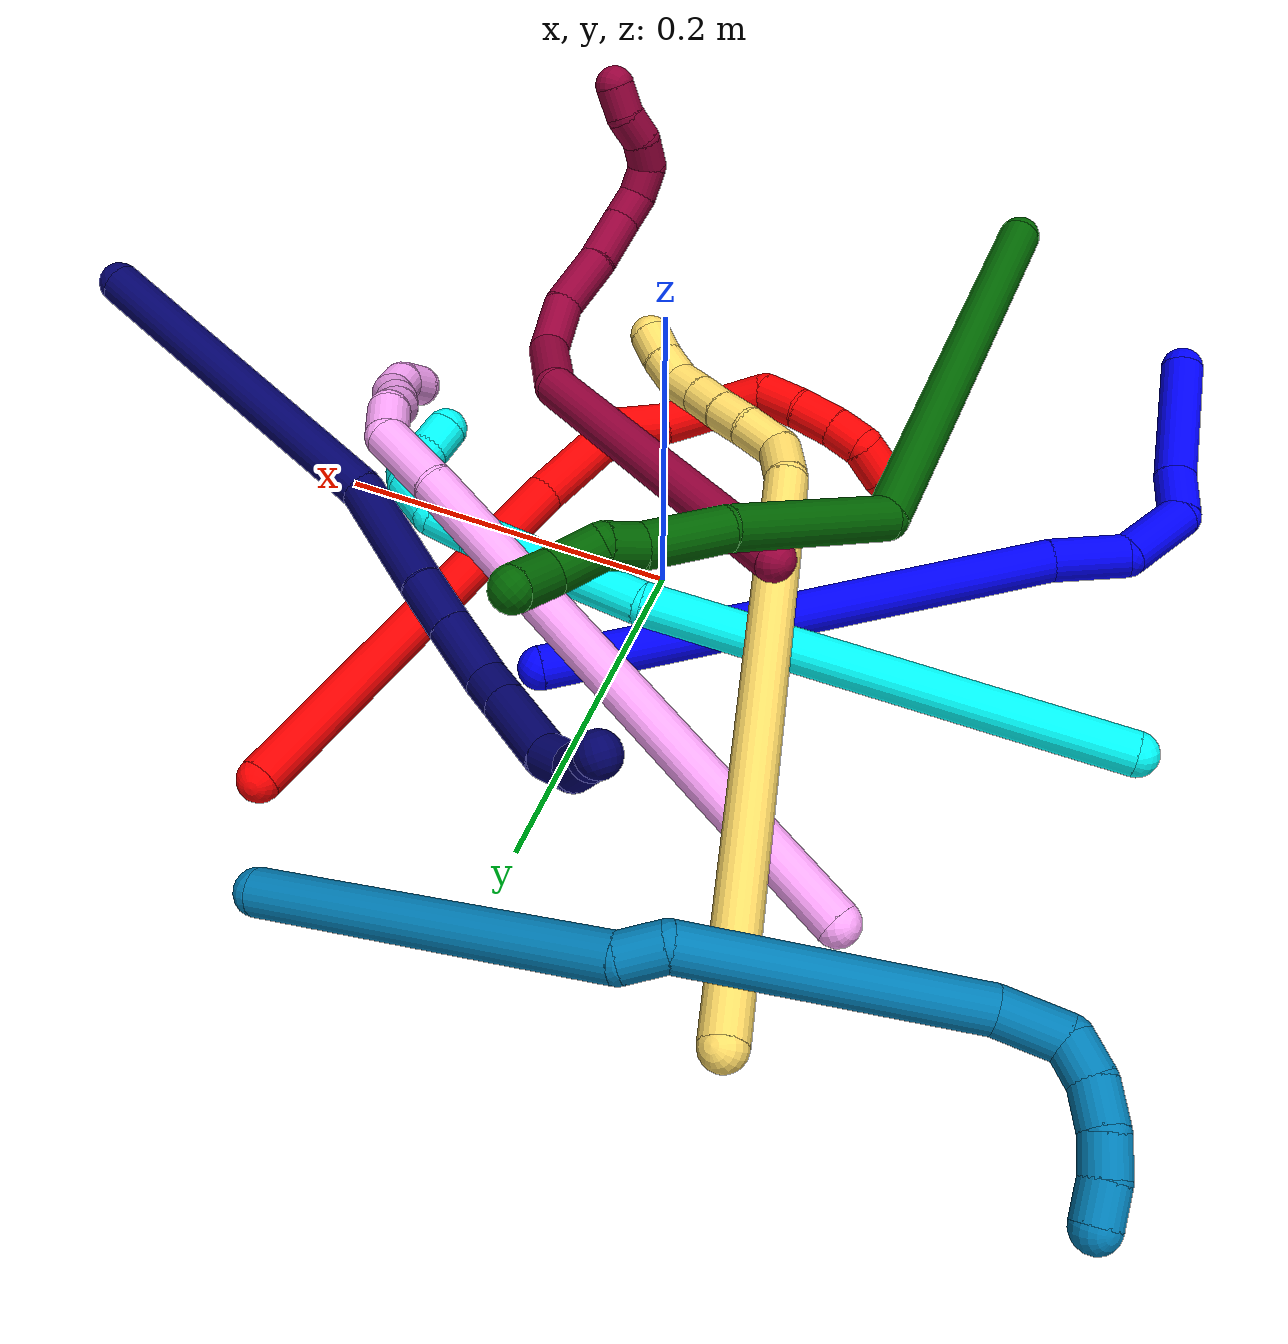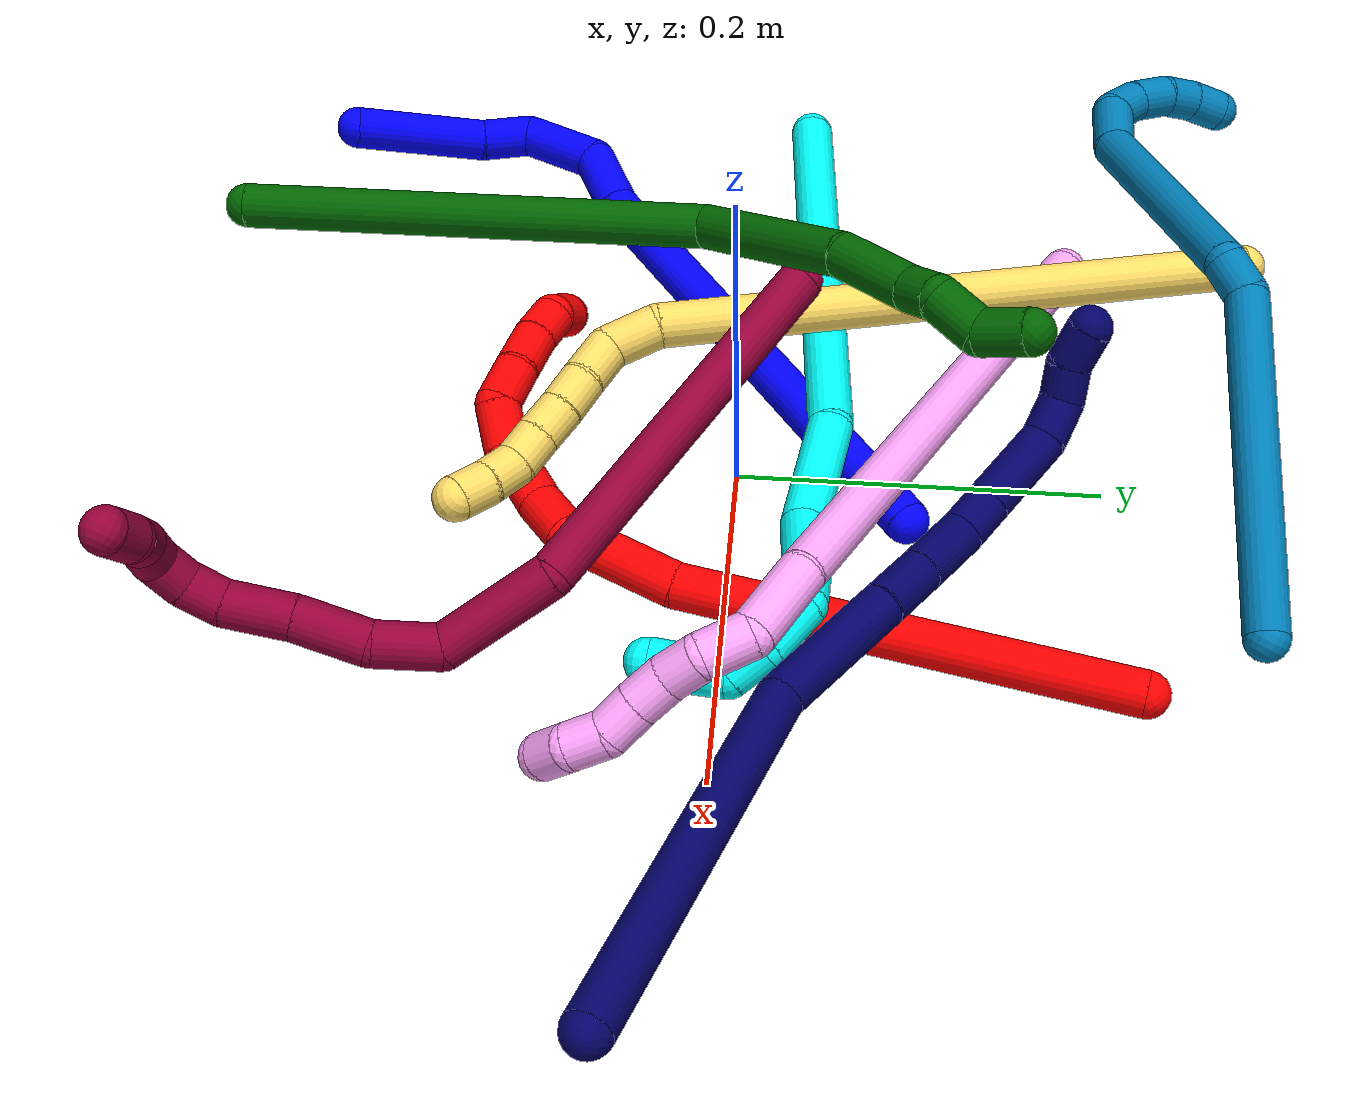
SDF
<sdf version="1.7">
 <world name="default">
  <plugin name="TubeGeneratorPlugin" filename="libtube_generator_plugin.so"/>
  <model name="photoneo_s_sensor">
   <static>1</static>
   <pose>0 0 2 1.57079 1.57079 3.14159</pose>
   <link name="link">
    <inertial><mass>0.1</mass></inertial>
    <sensor name="sensor" type="depth">
     <update_rate>30</update_rate>
     <camera>
      <horizontal_fov>1.22</horizontal_fov>
      <image><width>1920</width><height>1200</height><format>B8G8R8</format></image>
      <clip><near>0.1</near><far>4</far></clip>
      <depth_camera><output>points</output></depth_camera>
     </camera>
     <plugin name="camera_plugin" filename="libgazebo_ros_depth_camera.so">
      <baseline>0.2</baseline>
      <alwaysOn>1</alwaysOn>
      <updateRate>0.0</updateRate>
      <cameraName>camera_ir</cameraName>
      <imageTopicName>/camera/color/image_raw</imageTopicName>
      <cameraInfoTopicName>/camera/color/camera_info</cameraInfoTopicName>
      <depthImageTopicName>/camera/depth/image_raw</depthImageTopicName>
      <depthImageCameraInfoTopicName>/camera/depth/camera_info</depthImageCameraInfoTopicName>
      <pointCloudTopicName>/camera/depth/points</pointCloudTopicName>
      <frameName>fr_optical</frameName>
      <pointCloudCutoff>0.1</pointCloudCutoff>
      <pointCloudCutoffMax>2.0</pointCloudCutoffMax>
      <distortionK1>0</distortionK1>
      <distortionK2>0</distortionK2>
      <distortionK3>0</distortionK3>
      <distortionT1>0</distortionT1>
      <distortionT2>0</distortionT2>
      <CxPrime>0</CxPrime>
      <Cx>0</Cx>
      <Cy>0</Cy>
      <focalLength>0</focalLength>
      <hackBaseline>0</hackBaseline>
     </plugin>
    </sensor>
   </link>
  </model>
  <gravity>0 0 -9.8</gravity>
  <magnetic_field>6e-06 2.3e-05 -4.2e-05</magnetic_field>
  <atmosphere type="adiabatic"/>
  <physics name="default_physics" default="0" type="ode">
   <max_step_size>0.003</max_step_size>
   <real_time_factor>1</real_time_factor>
   <real_time_update_rate>1000</real_time_update_rate>
   <max_contacts>10000</max_contacts>
   <ode>
    <solver>
     <type>quick</type>
     <iters>100</iters>
     <sor>1.3</sor>
     <use_dynamic_moi_rescaling>0</use_dynamic_moi_rescaling>
    </solver>
    <constraints>
     <contact_max_correcting_vel>0</contact_max_correcting_vel>
     <contact_surface_layer>0.001</contact_surface_layer>
     <cfm>0</cfm>
     <erp>0.2</erp>
    </constraints>
   </ode>
  </physics>
  <scene><ambient>0.4 0.4 0.4 1</ambient><background>0.7 0.7 0.7 1</background><shadows>0</shadows></scene>
  <audio><device>default</device></audio>
  <spherical_coordinates>
   <surface_model>EARTH_WGS84</surface_model>
   <latitude_deg>0</latitude_deg>
   <longitude_deg>0</longitude_deg>
   <elevation>0</elevation>
   <heading_deg>0</heading_deg>
  </spherical_coordinates>
  <model name="bin">
   <static>1</static>
   <link name="bottom">
    <collision name="collision-bottom">
     <pose>0 0 -0.01 0 -0 0</pose>
     <geometry><box><size>0.8 0.6 0.02</size></box></geometry>
     <surface>
      <friction><ode><mu>100</mu><mu2>100</mu2></ode></friction>
      <contact><collide_bitmask>65535</collide_bitmask></contact>
     </surface>
    </collision>
   </link>
   <link name="west_wall">
    <collision name="collision-west_wall">
     <pose>-0.41 0 0.1 0 -0 0</pose>
     <geometry><box><size>0.02 0.6 0.2</size></box></geometry>
     <surface>
      <friction><ode><mu>100</mu><mu2>100</mu2></ode></friction>
      <contact><collide_bitmask>65535</collide_bitmask></contact>
     </surface>
    </collision>
   </link>
   <link name="east_wall">
    <collision name="collision-east_wall">
     <pose>0.41 0 0.1 0 -0 0</pose>
     <geometry><box><size>0.02 0.6 0.2</size></box></geometry>
     <surface>
      <friction><ode><mu>100</mu><mu2>100</mu2></ode></friction>
      <contact><collide_bitmask>65535</collide_bitmask></contact>
     </surface>
    </collision>
   </link>
   <link name="south_wall">
    <collision name="collision-south_wall">
     <pose>0 -0.31 0.1 0 -0 0</pose>
     <geometry><box><size>0.8 0.02 0.2</size></box></geometry>
     <surface>
      <friction><ode><mu>100</mu><mu2>100</mu2></ode></friction>
      <contact><collide_bitmask>65535</collide_bitmask></contact>
     </surface>
    </collision>
   </link>
   <link name="north_wall">
    <collision name="collision-north_wall">
     <pose>0 0.31 0.1 0 -0 0</pose>
     <geometry><box><size>0.8 0.02 0.2</size></box></geometry>
     <surface>
      <friction><ode><mu>100</mu><mu2>100</mu2></ode></friction>
      <contact><collide_bitmask>65535</collide_bitmask></contact>
     </surface>
    </collision>
   </link>
  </model>
  <model name="1">
   <static>0</static>
   <link name="1">
    <collision name="collision-cylinder-e_1_1_4">
     <pose>-0.087312 -0.042371 0.113708 0.356689 -0.623713 -0.116092</pose>
     <geometry><cylinder><radius>0.0125</radius><length>0.298986</length></cylinder></geometry>
     <surface>
      <friction><ode><mu>1.16</mu><mu2>1.16</mu2><slip1>0</slip1><slip2>0</slip2></ode></friction>
      <contact><ode><kp>1e+06</kp><kd>1</kd><max_vel>0</max_vel><min_depth>0.001</min_depth></ode></contact>
     </surface>
    </collision>
    <visual name="visual-cylinder-e_1_1_4">
     <pose>-0.087312 -0.042371 0.113708 0.356689 -0.623713 -0.116092</pose>
     <geometry><cylinder><radius>0.0125</radius><length>0.298986</length></cylinder></geometry>
     <material><ambient>0 0 1 1</ambient></material>
    </visual>
    <collision name="collision-cylinder-e_2_4_5">
     <pose>-0.183467 -0.092105 0.246315 0.371513 -0.411147 -0.078331</pose>
     <geometry><cylinder><radius>0.0125</radius><length>0.044254</length></cylinder></geometry>
     <surface>
      <friction><ode><mu>1.16</mu><mu2>1.16</mu2><slip1>0</slip1><slip2>0</slip2></ode></friction>
      <contact><ode><kp>1e+06</kp><kd>1</kd><max_vel>0</max_vel><min_depth>0.001</min_depth></ode></contact>
     </surface>
    </collision>
    <visual name="visual-cylinder-e_2_4_5">
     <pose>-0.183467 -0.092105 0.246315 0.371513 -0.411147 -0.078331</pose>
     <geometry><cylinder><radius>0.0125</radius><length>0.044254</length></cylinder></geometry>
     <material><ambient>0 0 1 1</ambient></material>
    </visual>
    <collision name="collision-cylinder-e_3_5_6">
     <pose>-0.213936 -0.103524 0.275835 0.36485 -1.08679 -0.221952</pose>
     <geometry><cylinder><radius>0.0125</radius><length>0.048866</length></cylinder></geometry>
     <surface>
      <friction><ode><mu>1.16</mu><mu2>1.16</mu2><slip1>0</slip1><slip2>0</slip2></ode></friction>
      <contact><ode><kp>1e+06</kp><kd>1</kd><max_vel>0</max_vel><min_depth>0.001</min_depth></ode></contact>
     </surface>
    </collision>
    <visual name="visual-cylinder-e_3_5_6">
     <pose>-0.213936 -0.103524 0.275835 0.36485 -1.08679 -0.221952</pose>
     <geometry><cylinder><radius>0.0125</radius><length>0.048866</length></cylinder></geometry>
     <material><ambient>0 0 1 1</ambient></material>
    </visual>
    <collision name="collision-cylinder-e_4_6_7">
     <pose>-0.249671 -0.108536 0.281746 2.94147 -1.24246 -2.86288</pose>
     <geometry><cylinder><radius>0.0125</radius><length>0.029808</length></cylinder></geometry>
     <surface>
      <friction><ode><mu>1.16</mu><mu2>1.16</mu2><slip1>0</slip1><slip2>0</slip2></ode></friction>
      <contact><ode><kp>1e+06</kp><kd>1</kd><max_vel>0</max_vel><min_depth>0.001</min_depth></ode></contact>
     </surface>
    </collision>
    <visual name="visual-cylinder-e_4_6_7">
     <pose>-0.249671 -0.108536 0.281746 2.94147 -1.24246 -2.86288</pose>
     <geometry><cylinder><radius>0.0125</radius><length>0.029808</length></cylinder></geometry>
     <material><ambient>0 0 1 1</ambient></material>
    </visual>
    <collision name="collision-cylinder-e_5_7_2">
     <pose>-0.300218 -0.119316 0.267031 2.36531 -1.20347 -2.06747</pose>
     <geometry><cylinder><radius>0.0125</radius><length>0.078087</length></cylinder></geometry>
     <surface>
      <friction><ode><mu>1.16</mu><mu2>1.16</mu2><slip1>0</slip1><slip2>0</slip2></ode></friction>
      <contact><ode><kp>1e+06</kp><kd>1</kd><max_vel>0</max_vel><min_depth>0.001</min_depth></ode></contact>
     </surface>
    </collision>
    <visual name="visual-cylinder-e_5_7_2">
     <pose>-0.300218 -0.119316 0.267031 2.36531 -1.20347 -2.06747</pose>
     <geometry><cylinder><radius>0.0125</radius><length>0.078087</length></cylinder></geometry>
     <material><ambient>0 0 1 1</ambient></material>
    </visual>
    <collision name="collision-sphere-2">
     <pose>-0.336657 -0.129139 0.257026 0 -0 0</pose>
     <geometry><sphere><radius>0.0125</radius></sphere></geometry>
     <surface>
      <friction><ode><mu>1.16</mu><mu2>1.16</mu2><slip1>0</slip1><slip2>0</slip2></ode></friction>
      <contact><ode><kp>1e+06</kp><kd>1</kd><max_vel>0</max_vel><min_depth>0.001</min_depth></ode></contact>
     </surface>
    </collision>
    <visual name="visual-sphere-2">
     <pose>-0.336657 -0.129139 0.257026 0 -0 0</pose>
     <geometry><sphere><radius>0.0125</radius></sphere></geometry>
     <material><ambient>0 0 1 1</ambient></material>
    </visual>
    <collision name="collision-sphere-7">
     <pose>-0.263779 -0.109492 0.277036 0 -0 0</pose>
     <geometry><sphere><radius>0.0125</radius></sphere></geometry>
     <surface>
      <friction><ode><mu>1.16</mu><mu2>1.16</mu2><slip1>0</slip1><slip2>0</slip2></ode></friction>
      <contact><ode><kp>1e+06</kp><kd>1</kd><max_vel>0</max_vel><min_depth>0.001</min_depth></ode></contact>
     </surface>
    </collision>
    <visual name="visual-sphere-7">
     <pose>-0.263779 -0.109492 0.277036 0 -0 0</pose>
     <geometry><sphere><radius>0.0125</radius></sphere></geometry>
     <material><ambient>0 0 1 1</ambient></material>
    </visual>
    <collision name="collision-sphere-6">
     <pose>-0.235563 -0.107581 0.286456 0 -0 0</pose>
     <geometry><sphere><radius>0.0125</radius></sphere></geometry>
     <surface>
      <friction><ode><mu>1.16</mu><mu2>1.16</mu2><slip1>0</slip1><slip2>0</slip2></ode></friction>
      <contact><ode><kp>1e+06</kp><kd>1</kd><max_vel>0</max_vel><min_depth>0.001</min_depth></ode></contact>
     </surface>
    </collision>
    <visual name="visual-sphere-6">
     <pose>-0.235563 -0.107581 0.286456 0 -0 0</pose>
     <geometry><sphere><radius>0.0125</radius></sphere></geometry>
     <material><ambient>0 0 1 1</ambient></material>
    </visual>
    <collision name="collision-sphere-5">
     <pose>-0.19231 -0.099468 0.265214 0 -0 0</pose>
     <geometry><sphere><radius>0.0125</radius></sphere></geometry>
     <surface>
      <friction><ode><mu>1.16</mu><mu2>1.16</mu2><slip1>0</slip1><slip2>0</slip2></ode></friction>
      <contact><ode><kp>1e+06</kp><kd>1</kd><max_vel>0</max_vel><min_depth>0.001</min_depth></ode></contact>
     </surface>
    </collision>
    <visual name="visual-sphere-5">
     <pose>-0.19231 -0.099468 0.265214 0 -0 0</pose>
     <geometry><sphere><radius>0.0125</radius></sphere></geometry>
     <material><ambient>0 0 1 1</ambient></material>
    </visual>
    <collision name="collision-sphere-1">
     <geometry><sphere><radius>0.0125</radius></sphere></geometry>
     <surface>
      <friction><ode><mu>1.16</mu><mu2>1.16</mu2><slip1>0</slip1><slip2>0</slip2></ode></friction>
      <contact><ode><kp>1e+06</kp><kd>1</kd><max_vel>0</max_vel><min_depth>0.001</min_depth></ode></contact>
     </surface>
    </collision>
    <visual name="visual-sphere-1">
     <geometry><sphere><radius>0.0125</radius></sphere></geometry>
     <material><ambient>0 0 1 1</ambient></material>
    </visual>
    <collision name="collision-sphere-4">
     <pose>-0.174623 -0.084741 0.227416 0 -0 0</pose>
     <geometry><sphere><radius>0.0125</radius></sphere></geometry>
     <surface>
      <friction><ode><mu>1.16</mu><mu2>1.16</mu2><slip1>0</slip1><slip2>0</slip2></ode></friction>
      <contact><ode><kp>1e+06</kp><kd>1</kd><max_vel>0</max_vel><min_depth>0.001</min_depth></ode></contact>
     </surface>
    </collision>
    <visual name="visual-sphere-4">
     <pose>-0.174623 -0.084741 0.227416 0 -0 0</pose>
     <geometry><sphere><radius>0.0125</radius></sphere></geometry>
     <material><ambient>0 0 1 1</ambient></material>
    </visual>
    <inertial>
     <pose>-0.151127 -0.06871 0.175252 0 -0 0</pose>
     <mass>0.5</mass>
     <inertia>
      <ixx>0.001558</ixx>
      <ixy>0</ixy>
      <ixz>0</ixz>
      <iyy>0.001963</iyy>
      <iyz>0</iyz>
      <izz>0.002035</izz>
     </inertia>
    </inertial>
   </link>
   <pose>0.034385 0.093791 0.011487 -1.86746 -0.079243 1.59748</pose>
  </model>
  <model name="2">
   <static>0</static>
   <link name="2">
    <collision name="collision-cylinder-e_1_1_4">
     <pose>0.000481 -0.071215 -0.101326 2.52896 0.003884 0.012282</pose>
     <geometry><cylinder><radius>0.0125</radius><length>0.247699</length></cylinder></geometry>
     <surface>
      <friction><ode><mu>1.16</mu><mu2>1.16</mu2><slip1>0</slip1><slip2>0</slip2></ode></friction>
      <contact><ode><kp>1e+06</kp><kd>1</kd><max_vel>0</max_vel><min_depth>0.001</min_depth></ode></contact>
     </surface>
    </collision>
    <visual name="visual-cylinder-e_1_1_4">
     <pose>0.000481 -0.071215 -0.101326 2.52896 0.003884 0.012282</pose>
     <geometry><cylinder><radius>0.0125</radius><length>0.247699</length></cylinder></geometry>
     <material><ambient>1 0 0 1</ambient></material>
    </visual>
    <collision name="collision-cylinder-e_2_4_5">
     <pose>-0.000549 -0.16577 -0.224491 2.323 -0.04725 -0.108835</pose>
     <geometry><cylinder><radius>0.0125</radius><length>0.063999</length></cylinder></geometry>
     <surface>
      <friction><ode><mu>1.16</mu><mu2>1.16</mu2><slip1>0</slip1><slip2>0</slip2></ode></friction>
      <contact><ode><kp>1e+06</kp><kd>1</kd><max_vel>0</max_vel><min_depth>0.001</min_depth></ode></contact>
     </surface>
    </collision>
    <visual name="visual-cylinder-e_2_4_5">
     <pose>-0.000549 -0.16577 -0.224491 2.323 -0.04725 -0.108835</pose>
     <geometry><cylinder><radius>0.0125</radius><length>0.063999</length></cylinder></geometry>
     <material><ambient>1 0 0 1</ambient></material>
    </visual>
    <collision name="collision-cylinder-e_3_5_6">
     <pose>-0.011099 -0.19872 -0.253413 2.20594 -0.648011 -1.17332</pose>
     <geometry><cylinder><radius>0.0125</radius><length>0.029948</length></cylinder></geometry>
     <surface>
      <friction><ode><mu>1.16</mu><mu2>1.16</mu2><slip1>0</slip1><slip2>0</slip2></ode></friction>
      <contact><ode><kp>1e+06</kp><kd>1</kd><max_vel>0</max_vel><min_depth>0.001</min_depth></ode></contact>
     </surface>
    </collision>
    <visual name="visual-cylinder-e_3_5_6">
     <pose>-0.011099 -0.19872 -0.253413 2.20594 -0.648011 -1.17332</pose>
     <geometry><cylinder><radius>0.0125</radius><length>0.029948</length></cylinder></geometry>
     <material><ambient>1 0 0 1</ambient></material>
    </visual>
    <collision name="collision-cylinder-e_4_6_7">
     <pose>-0.028547 -0.224157 -0.266135 1.91305 -0.464054 -0.646524</pose>
     <geometry><cylinder><radius>0.0125</radius><length>0.037577</length></cylinder></geometry>
     <surface>
      <friction><ode><mu>1.16</mu><mu2>1.16</mu2><slip1>0</slip1><slip2>0</slip2></ode></friction>
      <contact><ode><kp>1e+06</kp><kd>1</kd><max_vel>0</max_vel><min_depth>0.001</min_depth></ode></contact>
     </surface>
    </collision>
    <visual name="visual-cylinder-e_4_6_7">
     <pose>-0.028547 -0.224157 -0.266135 1.91305 -0.464054 -0.646524</pose>
     <geometry><cylinder><radius>0.0125</radius><length>0.037577</length></cylinder></geometry>
     <material><ambient>1 0 0 1</ambient></material>
    </visual>
    <collision name="collision-cylinder-e_5_7_8">
     <pose>-0.042327 -0.252184 -0.270628 1.47716 -0.413144 -0.377074</pose>
     <geometry><cylinder><radius>0.0125</radius><length>0.026757</length></cylinder></geometry>
     <surface>
      <friction><ode><mu>1.16</mu><mu2>1.16</mu2><slip1>0</slip1><slip2>0</slip2></ode></friction>
      <contact><ode><kp>1e+06</kp><kd>1</kd><max_vel>0</max_vel><min_depth>0.001</min_depth></ode></contact>
     </surface>
    </collision>
    <visual name="visual-cylinder-e_5_7_8">
     <pose>-0.042327 -0.252184 -0.270628 1.47716 -0.413144 -0.377074</pose>
     <geometry><cylinder><radius>0.0125</radius><length>0.026757</length></cylinder></geometry>
     <material><ambient>1 0 0 1</ambient></material>
    </visual>
    <collision name="collision-cylinder-e_6_8_9">
     <pose>-0.057416 -0.270583 -0.263791 0.82813 -0.857064 -0.396273</pose>
     <geometry><cylinder><radius>0.0125</radius><length>0.02571</length></cylinder></geometry>
     <surface>
      <friction><ode><mu>1.16</mu><mu2>1.16</mu2><slip1>0</slip1><slip2>0</slip2></ode></friction>
      <contact><ode><kp>1e+06</kp><kd>1</kd><max_vel>0</max_vel><min_depth>0.001</min_depth></ode></contact>
     </surface>
    </collision>
    <visual name="visual-cylinder-e_6_8_9">
     <pose>-0.057416 -0.270583 -0.263791 0.82813 -0.857064 -0.396273</pose>
     <geometry><cylinder><radius>0.0125</radius><length>0.02571</length></cylinder></geometry>
     <material><ambient>1 0 0 1</ambient></material>
    </visual>
    <collision name="collision-cylinder-e_7_9_10">
     <pose>-0.078033 -0.282024 -0.253881 0.893163 -1.0177 -0.522061</pose>
     <geometry><cylinder><radius>0.0125</radius><length>0.02562</length></cylinder></geometry>
     <surface>
      <friction><ode><mu>1.16</mu><mu2>1.16</mu2><slip1>0</slip1><slip2>0</slip2></ode></friction>
      <contact><ode><kp>1e+06</kp><kd>1</kd><max_vel>0</max_vel><min_depth>0.001</min_depth></ode></contact>
     </surface>
    </collision>
    <visual name="visual-cylinder-e_7_9_10">
     <pose>-0.078033 -0.282024 -0.253881 0.893163 -1.0177 -0.522061</pose>
     <geometry><cylinder><radius>0.0125</radius><length>0.02562</length></cylinder></geometry>
     <material><ambient>1 0 0 1</ambient></material>
    </visual>
    <collision name="collision-cylinder-e_8_10_11">
     <pose>-0.097918 -0.290498 -0.245375 0.645792 -1.03218 -0.375235</pose>
     <geometry><cylinder><radius>0.0125</radius><length>0.020934</length></cylinder></geometry>
     <surface>
      <friction><ode><mu>1.16</mu><mu2>1.16</mu2><slip1>0</slip1><slip2>0</slip2></ode></friction>
      <contact><ode><kp>1e+06</kp><kd>1</kd><max_vel>0</max_vel><min_depth>0.001</min_depth></ode></contact>
     </surface>
    </collision>
    <visual name="visual-cylinder-e_8_10_11">
     <pose>-0.097918 -0.290498 -0.245375 0.645792 -1.03218 -0.375235</pose>
     <geometry><cylinder><radius>0.0125</radius><length>0.020934</length></cylinder></geometry>
     <material><ambient>1 0 0 1</ambient></material>
    </visual>
    <collision name="collision-cylinder-e_9_11_2">
     <pose>-0.117637 -0.291993 -0.241389 -1.74326 -1.40808 1.58068</pose>
     <geometry><cylinder><radius>0.0125</radius><length>0.021756</length></cylinder></geometry>
     <surface>
      <friction><ode><mu>1.16</mu><mu2>1.16</mu2><slip1>0</slip1><slip2>0</slip2></ode></friction>
      <contact><ode><kp>1e+06</kp><kd>1</kd><max_vel>0</max_vel><min_depth>0.001</min_depth></ode></contact>
     </surface>
    </collision>
    <visual name="visual-cylinder-e_9_11_2">
     <pose>-0.117637 -0.291993 -0.241389 -1.74326 -1.40808 1.58068</pose>
     <geometry><cylinder><radius>0.0125</radius><length>0.021756</length></cylinder></geometry>
     <material><ambient>1 0 0 1</ambient></material>
    </visual>
    <collision name="collision-sphere-2">
     <pose>-0.128372 -0.290257 -0.241692 0 -0 0</pose>
     <geometry><sphere><radius>0.0125</radius></sphere></geometry>
     <surface>
      <friction><ode><mu>1.16</mu><mu2>1.16</mu2><slip1>0</slip1><slip2>0</slip2></ode></friction>
      <contact><ode><kp>1e+06</kp><kd>1</kd><max_vel>0</max_vel><min_depth>0.001</min_depth></ode></contact>
     </surface>
    </collision>
    <visual name="visual-sphere-2">
     <pose>-0.128372 -0.290257 -0.241692 0 -0 0</pose>
     <geometry><sphere><radius>0.0125</radius></sphere></geometry>
     <material><ambient>1 0 0 1</ambient></material>
    </visual>
    <collision name="collision-sphere-11">
     <pose>-0.106903 -0.293729 -0.241087 0 -0 0</pose>
     <geometry><sphere><radius>0.0125</radius></sphere></geometry>
     <surface>
      <friction><ode><mu>1.16</mu><mu2>1.16</mu2><slip1>0</slip1><slip2>0</slip2></ode></friction>
      <contact><ode><kp>1e+06</kp><kd>1</kd><max_vel>0</max_vel><min_depth>0.001</min_depth></ode></contact>
     </surface>
    </collision>
    <visual name="visual-sphere-11">
     <pose>-0.106903 -0.293729 -0.241087 0 -0 0</pose>
     <geometry><sphere><radius>0.0125</radius></sphere></geometry>
     <material><ambient>1 0 0 1</ambient></material>
    </visual>
    <collision name="collision-sphere-10">
     <pose>-0.088933 -0.287267 -0.249663 0 -0 0</pose>
     <geometry><sphere><radius>0.0125</radius></sphere></geometry>
     <surface>
      <friction><ode><mu>1.16</mu><mu2>1.16</mu2><slip1>0</slip1><slip2>0</slip2></ode></friction>
      <contact><ode><kp>1e+06</kp><kd>1</kd><max_vel>0</max_vel><min_depth>0.001</min_depth></ode></contact>
     </surface>
    </collision>
    <visual name="visual-sphere-10">
     <pose>-0.088933 -0.287267 -0.249663 0 -0 0</pose>
     <geometry><sphere><radius>0.0125</radius></sphere></geometry>
     <material><ambient>1 0 0 1</ambient></material>
    </visual>
    <collision name="collision-sphere-9">
     <pose>-0.067133 -0.276782 -0.2581 0 -0 0</pose>
     <geometry><sphere><radius>0.0125</radius></sphere></geometry>
     <surface>
      <friction><ode><mu>1.16</mu><mu2>1.16</mu2><slip1>0</slip1><slip2>0</slip2></ode></friction>
      <contact><ode><kp>1e+06</kp><kd>1</kd><max_vel>0</max_vel><min_depth>0.001</min_depth></ode></contact>
     </surface>
    </collision>
    <visual name="visual-sphere-9">
     <pose>-0.067133 -0.276782 -0.2581 0 -0 0</pose>
     <geometry><sphere><radius>0.0125</radius></sphere></geometry>
     <material><ambient>1 0 0 1</ambient></material>
    </visual>
    <collision name="collision-sphere-4">
     <pose>0.000962 -0.142431 -0.202651 0 -0 0</pose>
     <geometry><sphere><radius>0.0125</radius></sphere></geometry>
     <surface>
      <friction><ode><mu>1.16</mu><mu2>1.16</mu2><slip1>0</slip1><slip2>0</slip2></ode></friction>
      <contact><ode><kp>1e+06</kp><kd>1</kd><max_vel>0</max_vel><min_depth>0.001</min_depth></ode></contact>
     </surface>
    </collision>
    <visual name="visual-sphere-4">
     <pose>0.000962 -0.142431 -0.202651 0 -0 0</pose>
     <geometry><sphere><radius>0.0125</radius></sphere></geometry>
     <material><ambient>1 0 0 1</ambient></material>
    </visual>
    <collision name="collision-sphere-1">
     <geometry><sphere><radius>0.0125</radius></sphere></geometry>
     <surface>
      <friction><ode><mu>1.16</mu><mu2>1.16</mu2><slip1>0</slip1><slip2>0</slip2></ode></friction>
      <contact><ode><kp>1e+06</kp><kd>1</kd><max_vel>0</max_vel><min_depth>0.001</min_depth></ode></contact>
     </surface>
    </collision>
    <visual name="visual-sphere-1">
     <geometry><sphere><radius>0.0125</radius></sphere></geometry>
     <material><ambient>1 0 0 1</ambient></material>
    </visual>
    <collision name="collision-sphere-8">
     <pose>-0.047699 -0.264383 -0.269483 0 -0 0</pose>
     <geometry><sphere><radius>0.0125</radius></sphere></geometry>
     <surface>
      <friction><ode><mu>1.16</mu><mu2>1.16</mu2><slip1>0</slip1><slip2>0</slip2></ode></friction>
      <contact><ode><kp>1e+06</kp><kd>1</kd><max_vel>0</max_vel><min_depth>0.001</min_depth></ode></contact>
     </surface>
    </collision>
    <visual name="visual-sphere-8">
     <pose>-0.047699 -0.264383 -0.269483 0 -0 0</pose>
     <geometry><sphere><radius>0.0125</radius></sphere></geometry>
     <material><ambient>1 0 0 1</ambient></material>
    </visual>
    <collision name="collision-sphere-5">
     <pose>-0.002061 -0.18911 -0.24633 0 -0 0</pose>
     <geometry><sphere><radius>0.0125</radius></sphere></geometry>
     <surface>
      <friction><ode><mu>1.16</mu><mu2>1.16</mu2><slip1>0</slip1><slip2>0</slip2></ode></friction>
      <contact><ode><kp>1e+06</kp><kd>1</kd><max_vel>0</max_vel><min_depth>0.001</min_depth></ode></contact>
     </surface>
    </collision>
    <visual name="visual-sphere-5">
     <pose>-0.002061 -0.18911 -0.24633 0 -0 0</pose>
     <geometry><sphere><radius>0.0125</radius></sphere></geometry>
     <material><ambient>1 0 0 1</ambient></material>
    </visual>
    <collision name="collision-sphere-6">
     <pose>-0.020137 -0.20833 -0.260496 0 -0 0</pose>
     <geometry><sphere><radius>0.0125</radius></sphere></geometry>
     <surface>
      <friction><ode><mu>1.16</mu><mu2>1.16</mu2><slip1>0</slip1><slip2>0</slip2></ode></friction>
      <contact><ode><kp>1e+06</kp><kd>1</kd><max_vel>0</max_vel><min_depth>0.001</min_depth></ode></contact>
     </surface>
    </collision>
    <visual name="visual-sphere-6">
     <pose>-0.020137 -0.20833 -0.260496 0 -0 0</pose>
     <geometry><sphere><radius>0.0125</radius></sphere></geometry>
     <material><ambient>1 0 0 1</ambient></material>
    </visual>
    <collision name="collision-sphere-7">
     <pose>-0.036956 -0.239985 -0.271774 0 -0 0</pose>
     <geometry><sphere><radius>0.0125</radius></sphere></geometry>
     <surface>
      <friction><ode><mu>1.16</mu><mu2>1.16</mu2><slip1>0</slip1><slip2>0</slip2></ode></friction>
      <contact><ode><kp>1e+06</kp><kd>1</kd><max_vel>0</max_vel><min_depth>0.001</min_depth></ode></contact>
     </surface>
    </collision>
    <visual name="visual-sphere-7">
     <pose>-0.036956 -0.239985 -0.271774 0 -0 0</pose>
     <geometry><sphere><radius>0.0125</radius></sphere></geometry>
     <material><ambient>1 0 0 1</ambient></material>
    </visual>
    <inertial>
     <pose>-0.021076 -0.151974 -0.175942 0 -0 0</pose>
     <mass>0.5</mass>
     <inertia>
      <ixx>0.001306</ixx>
      <ixy>0</ixy>
      <ixz>0</ixz>
      <iyy>-0.001069</iyy>
      <iyz>0</iyz>
      <izz>0.000753</izz>
     </inertia>
    </inertial>
   </link>
   <pose>0.138661 0.216364 0.0115 -0.955588 -0.583851 -0.216199</pose>
  </model>
  <model name="3">
   <static>0</static>
   <link name="3">
    <collision name="collision-cylinder-e_1_1_4">
     <pose>0.118374 0.015882 0.066391 -0.234802 1.0477 -0.136058</pose>
     <geometry><cylinder><radius>0.0125</radius><length>0.273294</length></cylinder></geometry>
     <surface>
      <friction><ode><mu>1.16</mu><mu2>1.16</mu2><slip1>0</slip1><slip2>0</slip2></ode></friction>
      <contact><ode><kp>1e+06</kp><kd>1</kd><max_vel>0</max_vel><min_depth>0.001</min_depth></ode></contact>
     </surface>
    </collision>
    <visual name="visual-cylinder-e_1_1_4">
     <pose>0.118374 0.015882 0.066391 -0.234802 1.0477 -0.136058</pose>
     <geometry><cylinder><radius>0.0125</radius><length>0.273294</length></cylinder></geometry>
     <material><ambient>0.003922 1 0.996078 1</ambient></material>
    </visual>
    <collision name="collision-cylinder-e_2_4_5">
     <pose>0.26892 0.038157 0.139789 -0.739651 1.2841 -0.564272</pose>
     <geometry><cylinder><radius>0.0125</radius><length>0.067083</length></cylinder></geometry>
     <surface>
      <friction><ode><mu>1.16</mu><mu2>1.16</mu2><slip1>0</slip1><slip2>0</slip2></ode></friction>
      <contact><ode><kp>1e+06</kp><kd>1</kd><max_vel>0</max_vel><min_depth>0.001</min_depth></ode></contact>
     </surface>
    </collision>
    <visual name="visual-cylinder-e_2_4_5">
     <pose>0.26892 0.038157 0.139789 -0.739651 1.2841 -0.564272</pose>
     <geometry><cylinder><radius>0.0125</radius><length>0.067083</length></cylinder></geometry>
     <material><ambient>0.003922 1 0.996078 1</ambient></material>
    </visual>
    <collision name="collision-cylinder-e_3_5_6">
     <pose>0.319259 0.043805 0.158305 0.064636 1.00513 0.035535</pose>
     <geometry><cylinder><radius>0.0125</radius><length>0.043037</length></cylinder></geometry>
     <surface>
      <friction><ode><mu>1.16</mu><mu2>1.16</mu2><slip1>0</slip1><slip2>0</slip2></ode></friction>
      <contact><ode><kp>1e+06</kp><kd>1</kd><max_vel>0</max_vel><min_depth>0.001</min_depth></ode></contact>
     </surface>
    </collision>
    <visual name="visual-cylinder-e_3_5_6">
     <pose>0.319259 0.043805 0.158305 0.064636 1.00513 0.035535</pose>
     <geometry><cylinder><radius>0.0125</radius><length>0.043037</length></cylinder></geometry>
     <material><ambient>0.003922 1 0.996078 1</ambient></material>
    </visual>
    <collision name="collision-cylinder-e_4_6_7">
     <pose>0.347805 0.042669 0.174756 0.078869 1.12515 0.049746</pose>
     <geometry><cylinder><radius>0.0125</radius><length>0.023005</length></cylinder></geometry>
     <surface>
      <friction><ode><mu>1.16</mu><mu2>1.16</mu2><slip1>0</slip1><slip2>0</slip2></ode></friction>
      <contact><ode><kp>1e+06</kp><kd>1</kd><max_vel>0</max_vel><min_depth>0.001</min_depth></ode></contact>
     </surface>
    </collision>
    <visual name="visual-cylinder-e_4_6_7">
     <pose>0.347805 0.042669 0.174756 0.078869 1.12515 0.049746</pose>
     <geometry><cylinder><radius>0.0125</radius><length>0.023005</length></cylinder></geometry>
     <material><ambient>0.003922 1 0.996078 1</ambient></material>
    </visual>
    <collision name="collision-cylinder-e_5_7_8">
     <pose>0.373436 0.043095 0.176032 -2.92246 1.32931 -2.86263</pose>
     <geometry><cylinder><radius>0.0125</radius><length>0.031415</length></cylinder></geometry>
     <surface>
      <friction><ode><mu>1.16</mu><mu2>1.16</mu2><slip1>0</slip1><slip2>0</slip2></ode></friction>
      <contact><ode><kp>1e+06</kp><kd>1</kd><max_vel>0</max_vel><min_depth>0.001</min_depth></ode></contact>
     </surface>
    </collision>
    <visual name="visual-cylinder-e_5_7_8">
     <pose>0.373436 0.043095 0.176032 -2.92246 1.32931 -2.86263</pose>
     <geometry><cylinder><radius>0.0125</radius><length>0.031415</length></cylinder></geometry>
     <material><ambient>0.003922 1 0.996078 1</ambient></material>
    </visual>
    <collision name="collision-cylinder-e_6_8_9">
     <pose>0.396771 0.046331 0.165671 -2.79489 0.848836 -2.4022</pose>
     <geometry><cylinder><radius>0.0125</radius><length>0.021542</length></cylinder></geometry>
     <surface>
      <friction><ode><mu>1.16</mu><mu2>1.16</mu2><slip1>0</slip1><slip2>0</slip2></ode></friction>
      <contact><ode><kp>1e+06</kp><kd>1</kd><max_vel>0</max_vel><min_depth>0.001</min_depth></ode></contact>
     </surface>
    </collision>
    <visual name="visual-cylinder-e_6_8_9">
     <pose>0.396771 0.046331 0.165671 -2.79489 0.848836 -2.4022</pose>
     <geometry><cylinder><radius>0.0125</radius><length>0.021542</length></cylinder></geometry>
     <material><ambient>0.003922 1 0.996078 1</ambient></material>
    </visual>
    <collision name="collision-cylinder-e_7_9_10">
     <pose>0.407721 0.045647 0.149813 2.81517 0.288011 1.44396</pose>
     <geometry><cylinder><radius>0.0125</radius><length>0.020179</length></cylinder></geometry>
     <surface>
      <friction><ode><mu>1.16</mu><mu2>1.16</mu2><slip1>0</slip1><slip2>0</slip2></ode></friction>
      <contact><ode><kp>1e+06</kp><kd>1</kd><max_vel>0</max_vel><min_depth>0.001</min_depth></ode></contact>
     </surface>
    </collision>
    <visual name="visual-cylinder-e_7_9_10">
     <pose>0.407721 0.045647 0.149813 2.81517 0.288011 1.44396</pose>
     <geometry><cylinder><radius>0.0125</radius><length>0.020179</length></cylinder></geometry>
     <material><ambient>0.003922 1 0.996078 1</ambient></material>
    </visual>
    <collision name="collision-cylinder-e_8_10_2">
     <pose>0.413901 0.038466 0.131882 2.70615 0.33013 1.29082</pose>
     <geometry><cylinder><radius>0.0125</radius><length>0.020445</length></cylinder></geometry>
     <surface>
      <friction><ode><mu>1.16</mu><mu2>1.16</mu2><slip1>0</slip1><slip2>0</slip2></ode></friction>
      <contact><ode><kp>1e+06</kp><kd>1</kd><max_vel>0</max_vel><min_depth>0.001</min_depth></ode></contact>
     </surface>
    </collision>
    <visual name="visual-cylinder-e_8_10_2">
     <pose>0.413901 0.038466 0.131882 2.70615 0.33013 1.29082</pose>
     <geometry><cylinder><radius>0.0125</radius><length>0.020445</length></cylinder></geometry>
     <material><ambient>0.003922 1 0.996078 1</ambient></material>
    </visual>
    <collision name="collision-sphere-2">
     <pose>0.417214 0.034387 0.123114 0 -0 0</pose>
     <geometry><sphere><radius>0.0125</radius></sphere></geometry>
     <surface>
      <friction><ode><mu>1.16</mu><mu2>1.16</mu2><slip1>0</slip1><slip2>0</slip2></ode></friction>
      <contact><ode><kp>1e+06</kp><kd>1</kd><max_vel>0</max_vel><min_depth>0.001</min_depth></ode></contact>
     </surface>
    </collision>
    <visual name="visual-sphere-2">
     <pose>0.417214 0.034387 0.123114 0 -0 0</pose>
     <geometry><sphere><radius>0.0125</radius></sphere></geometry>
     <material><ambient>0.003922 1 0.996078 1</ambient></material>
    </visual>
    <collision name="collision-sphere-10">
     <pose>0.410587 0.042545 0.14065 0 -0 0</pose>
     <geometry><sphere><radius>0.0125</radius></sphere></geometry>
     <surface>
      <friction><ode><mu>1.16</mu><mu2>1.16</mu2><slip1>0</slip1><slip2>0</slip2></ode></friction>
      <contact><ode><kp>1e+06</kp><kd>1</kd><max_vel>0</max_vel><min_depth>0.001</min_depth></ode></contact>
     </surface>
    </collision>
    <visual name="visual-sphere-10">
     <pose>0.410587 0.042545 0.14065 0 -0 0</pose>
     <geometry><sphere><radius>0.0125</radius></sphere></geometry>
     <material><ambient>0.003922 1 0.996078 1</ambient></material>
    </visual>
    <collision name="collision-sphere-9">
     <pose>0.404855 0.048749 0.158977 0 -0 0</pose>
     <geometry><sphere><radius>0.0125</radius></sphere></geometry>
     <surface>
      <friction><ode><mu>1.16</mu><mu2>1.16</mu2><slip1>0</slip1><slip2>0</slip2></ode></friction>
      <contact><ode><kp>1e+06</kp><kd>1</kd><max_vel>0</max_vel><min_depth>0.001</min_depth></ode></contact>
     </surface>
    </collision>
    <visual name="visual-sphere-9">
     <pose>0.404855 0.048749 0.158977 0 -0 0</pose>
     <geometry><sphere><radius>0.0125</radius></sphere></geometry>
     <material><ambient>0.003922 1 0.996078 1</ambient></material>
    </visual>
    <collision name="collision-sphere-4">
     <pose>0.236748 0.031763 0.132782 0 -0 0</pose>
     <geometry><sphere><radius>0.0125</radius></sphere></geometry>
     <surface>
      <friction><ode><mu>1.16</mu><mu2>1.16</mu2><slip1>0</slip1><slip2>0</slip2></ode></friction>
      <contact><ode><kp>1e+06</kp><kd>1</kd><max_vel>0</max_vel><min_depth>0.001</min_depth></ode></contact>
     </surface>
    </collision>
    <visual name="visual-sphere-4">
     <pose>0.236748 0.031763 0.132782 0 -0 0</pose>
     <geometry><sphere><radius>0.0125</radius></sphere></geometry>
     <material><ambient>0.003922 1 0.996078 1</ambient></material>
    </visual>
    <collision name="collision-sphere-1">
     <geometry><sphere><radius>0.0125</radius></sphere></geometry>
     <surface>
      <friction><ode><mu>1.16</mu><mu2>1.16</mu2><slip1>0</slip1><slip2>0</slip2></ode></friction>
      <contact><ode><kp>1e+06</kp><kd>1</kd><max_vel>0</max_vel><min_depth>0.001</min_depth></ode></contact>
     </surface>
    </collision>
    <visual name="visual-sphere-1">
     <geometry><sphere><radius>0.0125</radius></sphere></geometry>
     <material><ambient>0.003922 1 0.996078 1</ambient></material>
    </visual>
    <collision name="collision-sphere-8">
     <pose>0.388687 0.043912 0.172366 0 -0 0</pose>
     <geometry><sphere><radius>0.0125</radius></sphere></geometry>
     <surface>
      <friction><ode><mu>1.16</mu><mu2>1.16</mu2><slip1>0</slip1><slip2>0</slip2></ode></friction>
      <contact><ode><kp>1e+06</kp><kd>1</kd><max_vel>0</max_vel><min_depth>0.001</min_depth></ode></contact>
     </surface>
    </collision>
    <visual name="visual-sphere-8">
     <pose>0.388687 0.043912 0.172366 0 -0 0</pose>
     <geometry><sphere><radius>0.0125</radius></sphere></geometry>
     <material><ambient>0.003922 1 0.996078 1</ambient></material>
    </visual>
    <collision name="collision-sphere-5">
     <pose>0.301093 0.04455 0.146795 0 -0 0</pose>
     <geometry><sphere><radius>0.0125</radius></sphere></geometry>
     <surface>
      <friction><ode><mu>1.16</mu><mu2>1.16</mu2><slip1>0</slip1><slip2>0</slip2></ode></friction>
      <contact><ode><kp>1e+06</kp><kd>1</kd><max_vel>0</max_vel><min_depth>0.001</min_depth></ode></contact>
     </surface>
    </collision>
    <visual name="visual-sphere-5">
     <pose>0.301093 0.04455 0.146795 0 -0 0</pose>
     <geometry><sphere><radius>0.0125</radius></sphere></geometry>
     <material><ambient>0.003922 1 0.996078 1</ambient></material>
    </visual>
    <collision name="collision-sphere-6">
     <pose>0.337426 0.04306 0.169814 0 -0 0</pose>
     <geometry><sphere><radius>0.0125</radius></sphere></geometry>
     <surface>
      <friction><ode><mu>1.16</mu><mu2>1.16</mu2><slip1>0</slip1><slip2>0</slip2></ode></friction>
      <contact><ode><kp>1e+06</kp><kd>1</kd><max_vel>0</max_vel><min_depth>0.001</min_depth></ode></contact>
     </surface>
    </collision>
    <visual name="visual-sphere-6">
     <pose>0.337426 0.04306 0.169814 0 -0 0</pose>
     <geometry><sphere><radius>0.0125</radius></sphere></geometry>
     <material><ambient>0.003922 1 0.996078 1</ambient></material>
    </visual>
    <collision name="collision-sphere-7">
     <pose>0.358184 0.042279 0.179699 0 -0 0</pose>
     <geometry><sphere><radius>0.0125</radius></sphere></geometry>
     <surface>
      <friction><ode><mu>1.16</mu><mu2>1.16</mu2><slip1>0</slip1><slip2>0</slip2></ode></friction>
      <contact><ode><kp>1e+06</kp><kd>1</kd><max_vel>0</max_vel><min_depth>0.001</min_depth></ode></contact>
     </surface>
    </collision>
    <visual name="visual-sphere-7">
     <pose>0.358184 0.042279 0.179699 0 -0 0</pose>
     <geometry><sphere><radius>0.0125</radius></sphere></geometry>
     <material><ambient>0.003922 1 0.996078 1</ambient></material>
    </visual>
    <inertial>
     <pose>0.218201 0.027653 0.106347 0 -0 0</pose>
     <mass>0.5</mass>
     <inertia>
      <ixx>0.000772</ixx>
      <ixy>0</ixy>
      <ixz>0</ixz>
      <iyy>0.001623</iyy>
      <iyz>0</iyz>
      <izz>-0.001718</izz>
     </inertia>
    </inertial>
   </link>
   <pose>-0.279231 0.027365 0.012396 -1.17902 -0.015751 -0.433602</pose>
  </model>
  <model name="4">
   <static>0</static>
   <link name="4">
    <collision name="collision-cylinder-e_1_1_4">
     <pose>0.080251 -0.090545 0.108972 0.693301 0.515368 0.189831</pose>
     <geometry><cylinder><radius>0.0125</radius><length>0.325659</length></cylinder></geometry>
     <surface>
      <friction><ode><mu>1.16</mu><mu2>1.16</mu2><slip1>0</slip1><slip2>0</slip2></ode></friction>
      <contact><ode><kp>1e+06</kp><kd>1</kd><max_vel>0</max_vel><min_depth>0.001</min_depth></ode></contact>
     </surface>
    </collision>
    <visual name="visual-cylinder-e_1_1_4">
     <pose>0.080251 -0.090545 0.108972 0.693301 0.515368 0.189831</pose>
     <geometry><cylinder><radius>0.0125</radius><length>0.325659</length></cylinder></geometry>
     <material><ambient>1 0.65098 0.996078 1</ambient></material>
    </visual>
    <collision name="collision-cylinder-e_2_4_5">
     <pose>0.171633 -0.19036 0.235775 0.479428 0.505745 0.126147</pose>
     <geometry><cylinder><radius>0.0125</radius><length>0.045948</length></cylinder></geometry>
     <surface>
      <friction><ode><mu>1.16</mu><mu2>1.16</mu2><slip1>0</slip1><slip2>0</slip2></ode></friction>
      <contact><ode><kp>1e+06</kp><kd>1</kd><max_vel>0</max_vel><min_depth>0.001</min_depth></ode></contact>
     </surface>
    </collision>
    <visual name="visual-cylinder-e_2_4_5">
     <pose>0.171633 -0.19036 0.235775 0.479428 0.505745 0.126147</pose>
     <geometry><cylinder><radius>0.0125</radius><length>0.045948</length></cylinder></geometry>
     <material><ambient>1 0.65098 0.996078 1</ambient></material>
    </visual>
    <collision name="collision-cylinder-e_3_5_6">
     <pose>0.193424 -0.198002 0.261582 -0.201379 0.918788 -0.099876</pose>
     <geometry><cylinder><radius>0.0125</radius><length>0.026827</length></cylinder></geometry>
     <surface>
      <friction><ode><mu>1.16</mu><mu2>1.16</mu2><slip1>0</slip1><slip2>0</slip2></ode></friction>
      <contact><ode><kp>1e+06</kp><kd>1</kd><max_vel>0</max_vel><min_depth>0.001</min_depth></ode></contact>
     </surface>
    </collision>
    <visual name="visual-cylinder-e_3_5_6">
     <pose>0.193424 -0.198002 0.261582 -0.201379 0.918788 -0.099876</pose>
     <geometry><cylinder><radius>0.0125</radius><length>0.026827</length></cylinder></geometry>
     <material><ambient>1 0.65098 0.996078 1</ambient></material>
    </visual>
    <collision name="collision-cylinder-e_4_6_7">
     <pose>0.209735 -0.191075 0.275956 -0.691666 0.597084 -0.220863</pose>
     <geometry><cylinder><radius>0.0125</radius><length>0.020095</length></cylinder></geometry>
     <surface>
      <friction><ode><mu>1.16</mu><mu2>1.16</mu2><slip1>0</slip1><slip2>0</slip2></ode></friction>
      <contact><ode><kp>1e+06</kp><kd>1</kd><max_vel>0</max_vel><min_depth>0.001</min_depth></ode></contact>
     </surface>
    </collision>
    <visual name="visual-cylinder-e_4_6_7">
     <pose>0.209735 -0.191075 0.275956 -0.691666 0.597084 -0.220863</pose>
     <geometry><cylinder><radius>0.0125</radius><length>0.020095</length></cylinder></geometry>
     <material><ambient>1 0.65098 0.996078 1</ambient></material>
    </visual>
    <collision name="collision-cylinder-e_5_7_8">
     <pose>0.220823 -0.182543 0.290269 -0.387794 0.566667 -0.114225</pose>
     <geometry><cylinder><radius>0.0125</radius><length>0.020262</length></cylinder></geometry>
     <surface>
      <friction><ode><mu>1.16</mu><mu2>1.16</mu2><slip1>0</slip1><slip2>0</slip2></ode></friction>
      <contact><ode><kp>1e+06</kp><kd>1</kd><max_vel>0</max_vel><min_depth>0.001</min_depth></ode></contact>
     </surface>
    </collision>
    <visual name="visual-cylinder-e_5_7_8">
     <pose>0.220823 -0.182543 0.290269 -0.387794 0.566667 -0.114225</pose>
     <geometry><cylinder><radius>0.0125</radius><length>0.020262</length></cylinder></geometry>
     <material><ambient>1 0.65098 0.996078 1</ambient></material>
    </visual>
    <collision name="collision-cylinder-e_6_8_9">
     <pose>0.231326 -0.17671 0.306593 -0.299804 0.521965 -0.080631</pose>
     <geometry><cylinder><radius>0.0125</radius><length>0.020313</length></cylinder></geometry>
     <surface>
      <friction><ode><mu>1.16</mu><mu2>1.16</mu2><slip1>0</slip1><slip2>0</slip2></ode></friction>
      <contact><ode><kp>1e+06</kp><kd>1</kd><max_vel>0</max_vel><min_depth>0.001</min_depth></ode></contact>
     </surface>
    </collision>
    <visual name="visual-cylinder-e_6_8_9">
     <pose>0.231326 -0.17671 0.306593 -0.299804 0.521965 -0.080631</pose>
     <geometry><cylinder><radius>0.0125</radius><length>0.020313</length></cylinder></geometry>
     <material><ambient>1 0.65098 0.996078 1</ambient></material>
    </visual>
    <collision name="collision-cylinder-e_7_9_10">
     <pose>0.244108 -0.169785 0.320291 -0.685628 0.84634 -0.31876</pose>
     <geometry><cylinder><radius>0.0125</radius><length>0.020614</length></cylinder></geometry>
     <surface>
      <friction><ode><mu>1.16</mu><mu2>1.16</mu2><slip1>0</slip1><slip2>0</slip2></ode></friction>
      <contact><ode><kp>1e+06</kp><kd>1</kd><max_vel>0</max_vel><min_depth>0.001</min_depth></ode></contact>
     </surface>
    </collision>
    <visual name="visual-cylinder-e_7_9_10">
     <pose>0.244108 -0.169785 0.320291 -0.685628 0.84634 -0.31876</pose>
     <geometry><cylinder><radius>0.0125</radius><length>0.020614</length></cylinder></geometry>
     <material><ambient>1 0.65098 0.996078 1</ambient></material>
    </visual>
    <collision name="collision-cylinder-e_8_10_2">
     <pose>0.256373 -0.157304 0.329534 -1.11923 0.464882 -0.294424</pose>
     <geometry><cylinder><radius>0.0125</radius><length>0.020282</length></cylinder></geometry>
     <surface>
      <friction><ode><mu>1.16</mu><mu2>1.16</mu2><slip1>0</slip1><slip2>0</slip2></ode></friction>
      <contact><ode><kp>1e+06</kp><kd>1</kd><max_vel>0</max_vel><min_depth>0.001</min_depth></ode></contact>
     </surface>
    </collision>
    <visual name="visual-cylinder-e_8_10_2">
     <pose>0.256373 -0.157304 0.329534 -1.11923 0.464882 -0.294424</pose>
     <geometry><cylinder><radius>0.0125</radius><length>0.020282</length></cylinder></geometry>
     <material><ambient>1 0.65098 0.996078 1</ambient></material>
    </visual>
    <collision name="collision-sphere-2">
     <pose>0.260919 -0.149148 0.33349 0 -0 0</pose>
     <geometry><sphere><radius>0.0125</radius></sphere></geometry>
     <surface>
      <friction><ode><mu>1.16</mu><mu2>1.16</mu2><slip1>0</slip1><slip2>0</slip2></ode></friction>
      <contact><ode><kp>1e+06</kp><kd>1</kd><max_vel>0</max_vel><min_depth>0.001</min_depth></ode></contact>
     </surface>
    </collision>
    <visual name="visual-sphere-2">
     <pose>0.260919 -0.149148 0.33349 0 -0 0</pose>
     <geometry><sphere><radius>0.0125</radius></sphere></geometry>
     <material><ambient>1 0.65098 0.996078 1</ambient></material>
    </visual>
    <collision name="collision-sphere-10">
     <pose>0.251826 -0.16546 0.325578 0 -0 0</pose>
     <geometry><sphere><radius>0.0125</radius></sphere></geometry>
     <surface>
      <friction><ode><mu>1.16</mu><mu2>1.16</mu2><slip1>0</slip1><slip2>0</slip2></ode></friction>
      <contact><ode><kp>1e+06</kp><kd>1</kd><max_vel>0</max_vel><min_depth>0.001</min_depth></ode></contact>
     </surface>
    </collision>
    <visual name="visual-sphere-10">
     <pose>0.251826 -0.16546 0.325578 0 -0 0</pose>
     <geometry><sphere><radius>0.0125</radius></sphere></geometry>
     <material><ambient>1 0.65098 0.996078 1</ambient></material>
    </visual>
    <collision name="collision-sphere-9">
     <pose>0.236389 -0.17411 0.315004 0 -0 0</pose>
     <geometry><sphere><radius>0.0125</radius></sphere></geometry>
     <surface>
      <friction><ode><mu>1.16</mu><mu2>1.16</mu2><slip1>0</slip1><slip2>0</slip2></ode></friction>
      <contact><ode><kp>1e+06</kp><kd>1</kd><max_vel>0</max_vel><min_depth>0.001</min_depth></ode></contact>
     </surface>
    </collision>
    <visual name="visual-sphere-9">
     <pose>0.236389 -0.17411 0.315004 0 -0 0</pose>
     <geometry><sphere><radius>0.0125</radius></sphere></geometry>
     <material><ambient>1 0.65098 0.996078 1</ambient></material>
    </visual>
    <collision name="collision-sphere-4">
     <pose>0.160503 -0.181089 0.217943 0 -0 0</pose>
     <geometry><sphere><radius>0.0125</radius></sphere></geometry>
     <surface>
      <friction><ode><mu>1.16</mu><mu2>1.16</mu2><slip1>0</slip1><slip2>0</slip2></ode></friction>
      <contact><ode><kp>1e+06</kp><kd>1</kd><max_vel>0</max_vel><min_depth>0.001</min_depth></ode></contact>
     </surface>
    </collision>
    <visual name="visual-sphere-4">
     <pose>0.160503 -0.181089 0.217943 0 -0 0</pose>
     <geometry><sphere><radius>0.0125</radius></sphere></geometry>
     <material><ambient>1 0.65098 0.996078 1</ambient></material>
    </visual>
    <collision name="collision-sphere-1">
     <geometry><sphere><radius>0.0125</radius></sphere></geometry>
     <surface>
      <friction><ode><mu>1.16</mu><mu2>1.16</mu2><slip1>0</slip1><slip2>0</slip2></ode></friction>
      <contact><ode><kp>1e+06</kp><kd>1</kd><max_vel>0</max_vel><min_depth>0.001</min_depth></ode></contact>
     </surface>
    </collision>
    <visual name="visual-sphere-1">
     <geometry><sphere><radius>0.0125</radius></sphere></geometry>
     <material><ambient>1 0.65098 0.996078 1</ambient></material>
    </visual>
    <collision name="collision-sphere-8">
     <pose>0.226262 -0.17931 0.298182 0 -0 0</pose>
     <geometry><sphere><radius>0.0125</radius></sphere></geometry>
     <surface>
      <friction><ode><mu>1.16</mu><mu2>1.16</mu2><slip1>0</slip1><slip2>0</slip2></ode></friction>
      <contact><ode><kp>1e+06</kp><kd>1</kd><max_vel>0</max_vel><min_depth>0.001</min_depth></ode></contact>
     </surface>
    </collision>
    <visual name="visual-sphere-8">
     <pose>0.226262 -0.17931 0.298182 0 -0 0</pose>
     <geometry><sphere><radius>0.0125</radius></sphere></geometry>
     <material><ambient>1 0.65098 0.996078 1</ambient></material>
    </visual>
    <collision name="collision-sphere-5">
     <pose>0.182763 -0.19963 0.253607 0 -0 0</pose>
     <geometry><sphere><radius>0.0125</radius></sphere></geometry>
     <surface>
      <friction><ode><mu>1.16</mu><mu2>1.16</mu2><slip1>0</slip1><slip2>0</slip2></ode></friction>
      <contact><ode><kp>1e+06</kp><kd>1</kd><max_vel>0</max_vel><min_depth>0.001</min_depth></ode></contact>
     </surface>
    </collision>
    <visual name="visual-sphere-5">
     <pose>0.182763 -0.19963 0.253607 0 -0 0</pose>
     <geometry><sphere><radius>0.0125</radius></sphere></geometry>
     <material><ambient>1 0.65098 0.996078 1</ambient></material>
    </visual>
    <collision name="collision-sphere-6">
     <pose>0.204086 -0.196374 0.269556 0 -0 0</pose>
     <geometry><sphere><radius>0.0125</radius></sphere></geometry>
     <surface>
      <friction><ode><mu>1.16</mu><mu2>1.16</mu2><slip1>0</slip1><slip2>0</slip2></ode></friction>
      <contact><ode><kp>1e+06</kp><kd>1</kd><max_vel>0</max_vel><min_depth>0.001</min_depth></ode></contact>
     </surface>
    </collision>
    <visual name="visual-sphere-6">
     <pose>0.204086 -0.196374 0.269556 0 -0 0</pose>
     <geometry><sphere><radius>0.0125</radius></sphere></geometry>
     <material><ambient>1 0.65098 0.996078 1</ambient></material>
    </visual>
    <collision name="collision-sphere-7">
     <pose>0.215384 -0.185775 0.282356 0 -0 0</pose>
     <geometry><sphere><radius>0.0125</radius></sphere></geometry>
     <surface>
      <friction><ode><mu>1.16</mu><mu2>1.16</mu2><slip1>0</slip1><slip2>0</slip2></ode></friction>
      <contact><ode><kp>1e+06</kp><kd>1</kd><max_vel>0</max_vel><min_depth>0.001</min_depth></ode></contact>
     </surface>
    </collision>
    <visual name="visual-sphere-7">
     <pose>0.215384 -0.185775 0.282356 0 -0 0</pose>
     <geometry><sphere><radius>0.0125</radius></sphere></geometry>
     <material><ambient>1 0.65098 0.996078 1</ambient></material>
    </visual>
    <inertial>
     <pose>0.125659 -0.122727 0.168558 0 -0 0</pose>
     <mass>0.5</mass>
     <inertia>
      <ixx>0.002981</ixx>
      <ixy>0</ixy>
      <ixz>0</ixz>
      <iyy>0.002836</iyy>
      <iyz>0</iyz>
      <izz>0.000198</izz>
     </inertia>
    </inertial>
   </link>
   <pose>-0.166555 0.183243 0.011486 -2.21535 -0.302723 -1.54488</pose>
  </model>
  <model name="5">
   <static>0</static>
   <link name="5">
    <collision name="collision-cylinder-e_1_1_4">
     <pose>0.090906 -0.127042 0.068123 1.07859 0.56263 0.342503</pose>
     <geometry><cylinder><radius>0.0125</radius><length>0.340848</length></cylinder></geometry>
     <surface>
      <friction><ode><mu>1.16</mu><mu2>1.16</mu2><slip1>0</slip1><slip2>0</slip2></ode></friction>
      <contact><ode><kp>1e+06</kp><kd>1</kd><max_vel>0</max_vel><min_depth>0.001</min_depth></ode></contact>
     </surface>
    </collision>
    <visual name="visual-cylinder-e_1_1_4">
     <pose>0.090906 -0.127042 0.068123 1.07859 0.56263 0.342503</pose>
     <geometry><cylinder><radius>0.0125</radius><length>0.340848</length></cylinder></geometry>
     <material><ambient>1 0.858824 0.4 1</ambient></material>
    </visual>
    <collision name="collision-cylinder-e_2_4_5">
     <pose>0.185406 -0.26644 0.143664 1.03018 0.244325 0.138773</pose>
     <geometry><cylinder><radius>0.0125</radius><length>0.029706</length></cylinder></geometry>
     <surface>
      <friction><ode><mu>1.16</mu><mu2>1.16</mu2><slip1>0</slip1><slip2>0</slip2></ode></friction>
      <contact><ode><kp>1e+06</kp><kd>1</kd><max_vel>0</max_vel><min_depth>0.001</min_depth></ode></contact>
     </surface>
    </collision>
    <visual name="visual-cylinder-e_2_4_5">
     <pose>0.185406 -0.26644 0.143664 1.03018 0.244325 0.138773</pose>
     <geometry><cylinder><radius>0.0125</radius><length>0.029706</length></cylinder></geometry>
     <material><ambient>1 0.858824 0.4 1</ambient></material>
    </visual>
    <collision name="collision-cylinder-e_3_5_6">
     <pose>0.186772 -0.292037 0.150668 1.60199 -0.166509 -0.17176</pose>
     <geometry><cylinder><radius>0.0125</radius><length>0.026865</length></cylinder></geometry>
     <surface>
      <friction><ode><mu>1.16</mu><mu2>1.16</mu2><slip1>0</slip1><slip2>0</slip2></ode></friction>
      <contact><ode><kp>1e+06</kp><kd>1</kd><max_vel>0</max_vel><min_depth>0.001</min_depth></ode></contact>
     </surface>
    </collision>
    <visual name="visual-cylinder-e_3_5_6">
     <pose>0.186772 -0.292037 0.150668 1.60199 -0.166509 -0.17176</pose>
     <geometry><cylinder><radius>0.0125</radius><length>0.026865</length></cylinder></geometry>
     <material><ambient>1 0.858824 0.4 1</ambient></material>
    </visual>
    <collision name="collision-cylinder-e_4_6_7">
     <pose>0.182294 -0.315737 0.151302 1.47098 -0.211045 -0.191093</pose>
     <geometry><cylinder><radius>0.0125</radius><length>0.021501</length></cylinder></geometry>
     <surface>
      <friction><ode><mu>1.16</mu><mu2>1.16</mu2><slip1>0</slip1><slip2>0</slip2></ode></friction>
      <contact><ode><kp>1e+06</kp><kd>1</kd><max_vel>0</max_vel><min_depth>0.001</min_depth></ode></contact>
     </surface>
    </collision>
    <visual name="visual-cylinder-e_4_6_7">
     <pose>0.182294 -0.315737 0.151302 1.47098 -0.211045 -0.191093</pose>
     <geometry><cylinder><radius>0.0125</radius><length>0.021501</length></cylinder></geometry>
     <material><ambient>1 0.858824 0.4 1</ambient></material>
    </visual>
    <collision name="collision-cylinder-e_5_7_8">
     <pose>0.178365 -0.33643 0.153948 1.41585 -0.160562 -0.137508</pose>
     <geometry><cylinder><radius>0.0125</radius><length>0.020985</length></cylinder></geometry>
     <surface>
      <friction><ode><mu>1.16</mu><mu2>1.16</mu2><slip1>0</slip1><slip2>0</slip2></ode></friction>
      <contact><ode><kp>1e+06</kp><kd>1</kd><max_vel>0</max_vel><min_depth>0.001</min_depth></ode></contact>
     </surface>
    </collision>
    <visual name="visual-cylinder-e_5_7_8">
     <pose>0.178365 -0.33643 0.153948 1.41585 -0.160562 -0.137508</pose>
     <geometry><cylinder><radius>0.0125</radius><length>0.020985</length></cylinder></geometry>
     <material><ambient>1 0.858824 0.4 1</ambient></material>
    </visual>
    <collision name="collision-cylinder-e_6_8_9">
     <pose>0.174816 -0.356389 0.156984 1.42408 -0.188044 -0.162419</pose>
     <geometry><cylinder><radius>0.0125</radius><length>0.020014</length></cylinder></geometry>
     <surface>
      <friction><ode><mu>1.16</mu><mu2>1.16</mu2><slip1>0</slip1><slip2>0</slip2></ode></friction>
      <contact><ode><kp>1e+06</kp><kd>1</kd><max_vel>0</max_vel><min_depth>0.001</min_depth></ode></contact>
     </surface>
    </collision>
    <visual name="visual-cylinder-e_6_8_9">
     <pose>0.174816 -0.356389 0.156984 1.42408 -0.188044 -0.162419</pose>
     <geometry><cylinder><radius>0.0125</radius><length>0.020014</length></cylinder></geometry>
     <material><ambient>1 0.858824 0.4 1</ambient></material>
    </visual>
    <collision name="collision-cylinder-e_7_9_10">
     <pose>0.173988 -0.376093 0.158716 1.54123 0.103989 0.100964</pose>
     <geometry><cylinder><radius>0.0125</radius><length>0.020075</length></cylinder></geometry>
     <surface>
      <friction><ode><mu>1.16</mu><mu2>1.16</mu2><slip1>0</slip1><slip2>0</slip2></ode></friction>
      <contact><ode><kp>1e+06</kp><kd>1</kd><max_vel>0</max_vel><min_depth>0.001</min_depth></ode></contact>
     </surface>
    </collision>
    <visual name="visual-cylinder-e_7_9_10">
     <pose>0.173988 -0.376093 0.158716 1.54123 0.103989 0.100964</pose>
     <geometry><cylinder><radius>0.0125</radius><length>0.020075</length></cylinder></geometry>
     <material><ambient>1 0.858824 0.4 1</ambient></material>
    </visual>
    <collision name="collision-cylinder-e_8_10_2">
     <pose>0.177173 -0.395818 0.159698 1.50038 0.215994 0.201399</pose>
     <geometry><cylinder><radius>0.0125</radius><length>0.020005</length></cylinder></geometry>
     <surface>
      <friction><ode><mu>1.16</mu><mu2>1.16</mu2><slip1>0</slip1><slip2>0</slip2></ode></friction>
      <contact><ode><kp>1e+06</kp><kd>1</kd><max_vel>0</max_vel><min_depth>0.001</min_depth></ode></contact>
     </surface>
    </collision>
    <visual name="visual-cylinder-e_8_10_2">
     <pose>0.177173 -0.395818 0.159698 1.50038 0.215994 0.201399</pose>
     <geometry><cylinder><radius>0.0125</radius><length>0.020005</length></cylinder></geometry>
     <material><ambient>1 0.858824 0.4 1</ambient></material>
    </visual>
    <collision name="collision-sphere-2">
     <pose>0.179317 -0.405564 0.160386 0 -0 0</pose>
     <geometry><sphere><radius>0.0125</radius></sphere></geometry>
     <surface>
      <friction><ode><mu>1.16</mu><mu2>1.16</mu2><slip1>0</slip1><slip2>0</slip2></ode></friction>
      <contact><ode><kp>1e+06</kp><kd>1</kd><max_vel>0</max_vel><min_depth>0.001</min_depth></ode></contact>
     </surface>
    </collision>
    <visual name="visual-sphere-2">
     <pose>0.179317 -0.405564 0.160386 0 -0 0</pose>
     <geometry><sphere><radius>0.0125</radius></sphere></geometry>
     <material><ambient>1 0.858824 0.4 1</ambient></material>
    </visual>
    <collision name="collision-sphere-10">
     <pose>0.17503 -0.386072 0.159011 0 -0 0</pose>
     <geometry><sphere><radius>0.0125</radius></sphere></geometry>
     <surface>
      <friction><ode><mu>1.16</mu><mu2>1.16</mu2><slip1>0</slip1><slip2>0</slip2></ode></friction>
      <contact><ode><kp>1e+06</kp><kd>1</kd><max_vel>0</max_vel><min_depth>0.001</min_depth></ode></contact>
     </surface>
    </collision>
    <visual name="visual-sphere-10">
     <pose>0.17503 -0.386072 0.159011 0 -0 0</pose>
     <geometry><sphere><radius>0.0125</radius></sphere></geometry>
     <material><ambient>1 0.858824 0.4 1</ambient></material>
    </visual>
    <collision name="collision-sphere-9">
     <pose>0.172946 -0.366114 0.158421 0 -0 0</pose>
     <geometry><sphere><radius>0.0125</radius></sphere></geometry>
     <surface>
      <friction><ode><mu>1.16</mu><mu2>1.16</mu2><slip1>0</slip1><slip2>0</slip2></ode></friction>
      <contact><ode><kp>1e+06</kp><kd>1</kd><max_vel>0</max_vel><min_depth>0.001</min_depth></ode></contact>
     </surface>
    </collision>
    <visual name="visual-sphere-9">
     <pose>0.172946 -0.366114 0.158421 0 -0 0</pose>
     <geometry><sphere><radius>0.0125</radius></sphere></geometry>
     <material><ambient>1 0.858824 0.4 1</ambient></material>
    </visual>
    <collision name="collision-sphere-4">
     <pose>0.181813 -0.254084 0.136247 0 -0 0</pose>
     <geometry><sphere><radius>0.0125</radius></sphere></geometry>
     <surface>
      <friction><ode><mu>1.16</mu><mu2>1.16</mu2><slip1>0</slip1><slip2>0</slip2></ode></friction>
      <contact><ode><kp>1e+06</kp><kd>1</kd><max_vel>0</max_vel><min_depth>0.001</min_depth></ode></contact>
     </surface>
    </collision>
    <visual name="visual-sphere-4">
     <pose>0.181813 -0.254084 0.136247 0 -0 0</pose>
     <geometry><sphere><radius>0.0125</radius></sphere></geometry>
     <material><ambient>1 0.858824 0.4 1</ambient></material>
    </visual>
    <collision name="collision-sphere-1">
     <geometry><sphere><radius>0.0125</radius></sphere></geometry>
     <surface>
      <friction><ode><mu>1.16</mu><mu2>1.16</mu2><slip1>0</slip1><slip2>0</slip2></ode></friction>
      <contact><ode><kp>1e+06</kp><kd>1</kd><max_vel>0</max_vel><min_depth>0.001</min_depth></ode></contact>
     </surface>
    </collision>
    <visual name="visual-sphere-1">
     <geometry><sphere><radius>0.0125</radius></sphere></geometry>
     <material><ambient>1 0.858824 0.4 1</ambient></material>
    </visual>
    <collision name="collision-sphere-8">
     <pose>0.176687 -0.346664 0.155547 0 -0 0</pose>
     <geometry><sphere><radius>0.0125</radius></sphere></geometry>
     <surface>
      <friction><ode><mu>1.16</mu><mu2>1.16</mu2><slip1>0</slip1><slip2>0</slip2></ode></friction>
      <contact><ode><kp>1e+06</kp><kd>1</kd><max_vel>0</max_vel><min_depth>0.001</min_depth></ode></contact>
     </surface>
    </collision>
    <visual name="visual-sphere-8">
     <pose>0.176687 -0.346664 0.155547 0 -0 0</pose>
     <geometry><sphere><radius>0.0125</radius></sphere></geometry>
     <material><ambient>1 0.858824 0.4 1</ambient></material>
    </visual>
    <collision name="collision-sphere-5">
     <pose>0.188999 -0.278797 0.151081 0 -0 0</pose>
     <geometry><sphere><radius>0.0125</radius></sphere></geometry>
     <surface>
      <friction><ode><mu>1.16</mu><mu2>1.16</mu2><slip1>0</slip1><slip2>0</slip2></ode></friction>
      <contact><ode><kp>1e+06</kp><kd>1</kd><max_vel>0</max_vel><min_depth>0.001</min_depth></ode></contact>
     </surface>
    </collision>
    <visual name="visual-sphere-5">
     <pose>0.188999 -0.278797 0.151081 0 -0 0</pose>
     <geometry><sphere><radius>0.0125</radius></sphere></geometry>
     <material><ambient>1 0.858824 0.4 1</ambient></material>
    </visual>
    <collision name="collision-sphere-6">
     <pose>0.184546 -0.305277 0.150254 0 -0 0</pose>
     <geometry><sphere><radius>0.0125</radius></sphere></geometry>
     <surface>
      <friction><ode><mu>1.16</mu><mu2>1.16</mu2><slip1>0</slip1><slip2>0</slip2></ode></friction>
      <contact><ode><kp>1e+06</kp><kd>1</kd><max_vel>0</max_vel><min_depth>0.001</min_depth></ode></contact>
     </surface>
    </collision>
    <visual name="visual-sphere-6">
     <pose>0.184546 -0.305277 0.150254 0 -0 0</pose>
     <geometry><sphere><radius>0.0125</radius></sphere></geometry>
     <material><ambient>1 0.858824 0.4 1</ambient></material>
    </visual>
    <collision name="collision-sphere-7">
     <pose>0.180042 -0.326197 0.15235 0 -0 0</pose>
     <geometry><sphere><radius>0.0125</radius></sphere></geometry>
     <surface>
      <friction><ode><mu>1.16</mu><mu2>1.16</mu2><slip1>0</slip1><slip2>0</slip2></ode></friction>
      <contact><ode><kp>1e+06</kp><kd>1</kd><max_vel>0</max_vel><min_depth>0.001</min_depth></ode></contact>
     </surface>
    </collision>
    <visual name="visual-sphere-7">
     <pose>0.180042 -0.326197 0.15235 0 -0 0</pose>
     <geometry><sphere><radius>0.0125</radius></sphere></geometry>
     <material><ambient>1 0.858824 0.4 1</ambient></material>
    </visual>
    <inertial>
     <pose>0.119418 -0.191025 0.095084 0 -0 0</pose>
     <mass>0.5</mass>
     <inertia>
      <ixx>0.003608</ixx>
      <ixy>0</ixy>
      <ixz>0</ixz>
      <iyy>0.00291</iyy>
      <iyz>0</iyz>
      <izz>0.000728</izz>
     </inertia>
    </inertial>
   </link>
   <pose>-0.143241 0.281464 0.04254 -3.06909 -0.653265 -2.19277</pose>
  </model>
  <model name="6">
   <static>0</static>
   <link name="6">
    <collision name="collision-cylinder-e_1_1_4">
     <pose>-0.0597 0.064491 -0.097639 -2.55787 -0.471768 1.34951</pose>
     <geometry><cylinder><radius>0.0125</radius><length>0.262728</length></cylinder></geometry>
     <surface>
      <friction><ode><mu>1.16</mu><mu2>1.16</mu2><slip1>0</slip1><slip2>0</slip2></ode></friction>
      <contact><ode><kp>1e+06</kp><kd>1</kd><max_vel>0</max_vel><min_depth>0.001</min_depth></ode></contact>
     </surface>
    </collision>
    <visual name="visual-cylinder-e_1_1_4">
     <pose>-0.0597 0.064491 -0.097639 -2.55787 -0.471768 1.34951</pose>
     <geometry><cylinder><radius>0.0125</radius><length>0.262728</length></cylinder></geometry>
     <material><ambient>0 0.392157 0.003922 1</ambient></material>
    </visual>
    <collision name="collision-cylinder-e_2_4_5">
     <pose>-0.105793 0.168845 -0.230328 -2.29201 0.250935 -0.543875</pose>
     <geometry><cylinder><radius>0.0125</radius><length>0.109594</length></cylinder></geometry>
     <surface>
      <friction><ode><mu>1.16</mu><mu2>1.16</mu2><slip1>0</slip1><slip2>0</slip2></ode></friction>
      <contact><ode><kp>1e+06</kp><kd>1</kd><max_vel>0</max_vel><min_depth>0.001</min_depth></ode></contact>
     </surface>
    </collision>
    <visual name="visual-cylinder-e_2_4_5">
     <pose>-0.105793 0.168845 -0.230328 -2.29201 0.250935 -0.543875</pose>
     <geometry><cylinder><radius>0.0125</radius><length>0.109594</length></cylinder></geometry>
     <material><ambient>0 0.392157 0.003922 1</ambient></material>
    </visual>
    <collision name="collision-cylinder-e_3_5_6">
     <pose>-0.085436 0.222612 -0.284864 -2.52188 0.27488 -0.815567</pose>
     <geometry><cylinder><radius>0.0125</radius><length>0.049744</length></cylinder></geometry>
     <surface>
      <friction><ode><mu>1.16</mu><mu2>1.16</mu2><slip1>0</slip1><slip2>0</slip2></ode></friction>
      <contact><ode><kp>1e+06</kp><kd>1</kd><max_vel>0</max_vel><min_depth>0.001</min_depth></ode></contact>
     </surface>
    </collision>
    <visual name="visual-cylinder-e_3_5_6">
     <pose>-0.085436 0.222612 -0.284864 -2.52188 0.27488 -0.815567</pose>
     <geometry><cylinder><radius>0.0125</radius><length>0.049744</length></cylinder></geometry>
     <material><ambient>0 0.392157 0.003922 1</ambient></material>
    </visual>
    <collision name="collision-cylinder-e_4_6_7">
     <pose>-0.07495 0.243936 -0.310957 -2.29821 0.35957 -0.769862</pose>
     <geometry><cylinder><radius>0.0125</radius><length>0.021228</length></cylinder></geometry>
     <surface>
      <friction><ode><mu>1.16</mu><mu2>1.16</mu2><slip1>0</slip1><slip2>0</slip2></ode></friction>
      <contact><ode><kp>1e+06</kp><kd>1</kd><max_vel>0</max_vel><min_depth>0.001</min_depth></ode></contact>
     </surface>
    </collision>
    <visual name="visual-cylinder-e_4_6_7">
     <pose>-0.07495 0.243936 -0.310957 -2.29821 0.35957 -0.769862</pose>
     <geometry><cylinder><radius>0.0125</radius><length>0.021228</length></cylinder></geometry>
     <material><ambient>0 0.392157 0.003922 1</ambient></material>
    </visual>
    <collision name="collision-cylinder-e_5_7_8">
     <pose>-0.068762 0.254923 -0.331172 -2.88524 0.17262 -1.18249</pose>
     <geometry><cylinder><radius>0.0125</radius><length>0.028562</length></cylinder></geometry>
     <surface>
      <friction><ode><mu>1.16</mu><mu2>1.16</mu2><slip1>0</slip1><slip2>0</slip2></ode></friction>
      <contact><ode><kp>1e+06</kp><kd>1</kd><max_vel>0</max_vel><min_depth>0.001</min_depth></ode></contact>
     </surface>
    </collision>
    <visual name="visual-cylinder-e_5_7_8">
     <pose>-0.068762 0.254923 -0.331172 -2.88524 0.17262 -1.18249</pose>
     <geometry><cylinder><radius>0.0125</radius><length>0.028562</length></cylinder></geometry>
     <material><ambient>0 0.392157 0.003922 1</ambient></material>
    </visual>
    <collision name="collision-cylinder-e_6_8_2">
     <pose>-0.067512 0.269329 -0.353675 -2.25798 -0.085592 0.180579</pose>
     <geometry><cylinder><radius>0.0125</radius><length>0.028144</length></cylinder></geometry>
     <surface>
      <friction><ode><mu>1.16</mu><mu2>1.16</mu2><slip1>0</slip1><slip2>0</slip2></ode></friction>
      <contact><ode><kp>1e+06</kp><kd>1</kd><max_vel>0</max_vel><min_depth>0.001</min_depth></ode></contact>
     </surface>
    </collision>
    <visual name="visual-cylinder-e_6_8_2">
     <pose>-0.067512 0.269329 -0.353675 -2.25798 -0.085592 0.180579</pose>
     <geometry><cylinder><radius>0.0125</radius><length>0.028144</length></cylinder></geometry>
     <material><ambient>0 0.392157 0.003922 1</ambient></material>
    </visual>
    <collision name="collision-sphere-2">
     <pose>-0.068715 0.280167 -0.362569 0 -0 0</pose>
     <geometry><sphere><radius>0.0125</radius></sphere></geometry>
     <surface>
      <friction><ode><mu>1.16</mu><mu2>1.16</mu2><slip1>0</slip1><slip2>0</slip2></ode></friction>
      <contact><ode><kp>1e+06</kp><kd>1</kd><max_vel>0</max_vel><min_depth>0.001</min_depth></ode></contact>
     </surface>
    </collision>
    <visual name="visual-sphere-2">
     <pose>-0.068715 0.280167 -0.362569 0 -0 0</pose>
     <geometry><sphere><radius>0.0125</radius></sphere></geometry>
     <material><ambient>0 0.392157 0.003922 1</ambient></material>
    </visual>
    <collision name="collision-sphere-4">
     <pose>-0.1194 0.128981 -0.195279 0 -0 0</pose>
     <geometry><sphere><radius>0.0125</radius></sphere></geometry>
     <surface>
      <friction><ode><mu>1.16</mu><mu2>1.16</mu2><slip1>0</slip1><slip2>0</slip2></ode></friction>
      <contact><ode><kp>1e+06</kp><kd>1</kd><max_vel>0</max_vel><min_depth>0.001</min_depth></ode></contact>
     </surface>
    </collision>
    <visual name="visual-sphere-4">
     <pose>-0.1194 0.128981 -0.195279 0 -0 0</pose>
     <geometry><sphere><radius>0.0125</radius></sphere></geometry>
     <material><ambient>0 0.392157 0.003922 1</ambient></material>
    </visual>
    <collision name="collision-sphere-1">
     <geometry><sphere><radius>0.0125</radius></sphere></geometry>
     <surface>
      <friction><ode><mu>1.16</mu><mu2>1.16</mu2><slip1>0</slip1><slip2>0</slip2></ode></friction>
      <contact><ode><kp>1e+06</kp><kd>1</kd><max_vel>0</max_vel><min_depth>0.001</min_depth></ode></contact>
     </surface>
    </collision>
    <visual name="visual-sphere-1">
     <geometry><sphere><radius>0.0125</radius></sphere></geometry>
     <material><ambient>0 0.392157 0.003922 1</ambient></material>
    </visual>
    <collision name="collision-sphere-8">
     <pose>-0.066309 0.25849 -0.344781 0 -0 0</pose>
     <geometry><sphere><radius>0.0125</radius></sphere></geometry>
     <surface>
      <friction><ode><mu>1.16</mu><mu2>1.16</mu2><slip1>0</slip1><slip2>0</slip2></ode></friction>
      <contact><ode><kp>1e+06</kp><kd>1</kd><max_vel>0</max_vel><min_depth>0.001</min_depth></ode></contact>
     </surface>
    </collision>
    <visual name="visual-sphere-8">
     <pose>-0.066309 0.25849 -0.344781 0 -0 0</pose>
     <geometry><sphere><radius>0.0125</radius></sphere></geometry>
     <material><ambient>0 0.392157 0.003922 1</ambient></material>
    </visual>
    <collision name="collision-sphere-5">
     <pose>-0.092187 0.208709 -0.265377 0 -0 0</pose>
     <geometry><sphere><radius>0.0125</radius></sphere></geometry>
     <surface>
      <friction><ode><mu>1.16</mu><mu2>1.16</mu2><slip1>0</slip1><slip2>0</slip2></ode></friction>
      <contact><ode><kp>1e+06</kp><kd>1</kd><max_vel>0</max_vel><min_depth>0.001</min_depth></ode></contact>
     </surface>
    </collision>
    <visual name="visual-sphere-5">
     <pose>-0.092187 0.208709 -0.265377 0 -0 0</pose>
     <geometry><sphere><radius>0.0125</radius></sphere></geometry>
     <material><ambient>0 0.392157 0.003922 1</ambient></material>
    </visual>
    <collision name="collision-sphere-6">
     <pose>-0.078685 0.236515 -0.304351 0 -0 0</pose>
     <geometry><sphere><radius>0.0125</radius></sphere></geometry>
     <surface>
      <friction><ode><mu>1.16</mu><mu2>1.16</mu2><slip1>0</slip1><slip2>0</slip2></ode></friction>
      <contact><ode><kp>1e+06</kp><kd>1</kd><max_vel>0</max_vel><min_depth>0.001</min_depth></ode></contact>
     </surface>
    </collision>
    <visual name="visual-sphere-6">
     <pose>-0.078685 0.236515 -0.304351 0 -0 0</pose>
     <geometry><sphere><radius>0.0125</radius></sphere></geometry>
     <material><ambient>0 0.392157 0.003922 1</ambient></material>
    </visual>
    <collision name="collision-sphere-7">
     <pose>-0.071215 0.251356 -0.317563 0 -0 0</pose>
     <geometry><sphere><radius>0.0125</radius></sphere></geometry>
     <surface>
      <friction><ode><mu>1.16</mu><mu2>1.16</mu2><slip1>0</slip1><slip2>0</slip2></ode></friction>
      <contact><ode><kp>1e+06</kp><kd>1</kd><max_vel>0</max_vel><min_depth>0.001</min_depth></ode></contact>
     </surface>
    </collision>
    <visual name="visual-sphere-7">
     <pose>-0.071215 0.251356 -0.317563 0 -0 0</pose>
     <geometry><sphere><radius>0.0125</radius></sphere></geometry>
     <material><ambient>0 0.392157 0.003922 1</ambient></material>
    </visual>
    <inertial>
     <pose>-0.073968 0.133122 -0.182158 0 -0 0</pose>
     <mass>0.5</mass>
     <inertia>
      <ixx>0.001653</ixx>
      <ixy>0</ixy>
      <ixz>0</ixz>
      <iyy>0.001306</iyy>
      <iyz>0</iyz>
      <izz>-0.00021</izz>
     </inertia>
    </inertial>
   </link>
   <pose>-0.122059 -0.288355 0.072302 1.09955 -0.188151 -0.494706</pose>
  </model>
  <model name="7">
   <static>0</static>
   <link name="7">
    <collision name="collision-cylinder-e_1_1_4">
     <pose>-0.058438 -0.004374 -0.088133 3.09201 -0.58494 -2.97725</pose>
     <geometry><cylinder><radius>0.0125</radius><length>0.211675</length></cylinder></geometry>
     <surface>
      <friction><ode><mu>1.16</mu><mu2>1.16</mu2><slip1>0</slip1><slip2>0</slip2></ode></friction>
      <contact><ode><kp>1e+06</kp><kd>1</kd><max_vel>0</max_vel><min_depth>0.001</min_depth></ode></contact>
     </surface>
    </collision>
    <visual name="visual-cylinder-e_1_1_4">
     <pose>-0.058438 -0.004374 -0.088133 3.09201 -0.58494 -2.97725</pose>
     <geometry><cylinder><radius>0.0125</radius><length>0.211675</length></cylinder></geometry>
     <material><ambient>0.003922 0 0.403922 1</ambient></material>
    </visual>
    <collision name="collision-cylinder-e_2_4_5">
     <pose>-0.133554 0.002266 -0.210212 -2.82786 -0.437178 1.9041</pose>
     <geometry><cylinder><radius>0.0125</radius><length>0.078785</length></cylinder></geometry>
     <surface>
      <friction><ode><mu>1.16</mu><mu2>1.16</mu2><slip1>0</slip1><slip2>0</slip2></ode></friction>
      <contact><ode><kp>1e+06</kp><kd>1</kd><max_vel>0</max_vel><min_depth>0.001</min_depth></ode></contact>
     </surface>
    </collision>
    <visual name="visual-cylinder-e_2_4_5">
     <pose>-0.133554 0.002266 -0.210212 -2.82786 -0.437178 1.9041</pose>
     <geometry><cylinder><radius>0.0125</radius><length>0.078785</length></cylinder></geometry>
     <material><ambient>0.003922 0 0.403922 1</ambient></material>
    </visual>
    <collision name="collision-cylinder-e_3_5_6">
     <pose>-0.156795 0.016355 -0.258665 -2.93275 -0.416604 2.22097</pose>
     <geometry><cylinder><radius>0.0125</radius><length>0.032432</length></cylinder></geometry>
     <surface>
      <friction><ode><mu>1.16</mu><mu2>1.16</mu2><slip1>0</slip1><slip2>0</slip2></ode></friction>
      <contact><ode><kp>1e+06</kp><kd>1</kd><max_vel>0</max_vel><min_depth>0.001</min_depth></ode></contact>
     </surface>
    </collision>
    <visual name="visual-cylinder-e_3_5_6">
     <pose>-0.156795 0.016355 -0.258665 -2.93275 -0.416604 2.22097</pose>
     <geometry><cylinder><radius>0.0125</radius><length>0.032432</length></cylinder></geometry>
     <material><ambient>0.003922 0 0.403922 1</ambient></material>
    </visual>
    <collision name="collision-cylinder-e_4_6_7">
     <pose>-0.171326 0.022601 -0.290727 -2.96285 -0.420096 2.3458</pose>
     <geometry><cylinder><radius>0.0125</radius><length>0.039078</length></cylinder></geometry>
     <surface>
      <friction><ode><mu>1.16</mu><mu2>1.16</mu2><slip1>0</slip1><slip2>0</slip2></ode></friction>
      <contact><ode><kp>1e+06</kp><kd>1</kd><max_vel>0</max_vel><min_depth>0.001</min_depth></ode></contact>
     </surface>
    </collision>
    <visual name="visual-cylinder-e_4_6_7">
     <pose>-0.171326 0.022601 -0.290727 -2.96285 -0.420096 2.3458</pose>
     <geometry><cylinder><radius>0.0125</radius><length>0.039078</length></cylinder></geometry>
     <material><ambient>0.003922 0 0.403922 1</ambient></material>
    </visual>
    <collision name="collision-cylinder-e_5_7_8">
     <pose>-0.185656 0.030856 -0.316444 -2.58449 -0.584568 1.62161</pose>
     <geometry><cylinder><radius>0.0125</radius><length>0.023057</length></cylinder></geometry>
     <surface>
      <friction><ode><mu>1.16</mu><mu2>1.16</mu2><slip1>0</slip1><slip2>0</slip2></ode></friction>
      <contact><ode><kp>1e+06</kp><kd>1</kd><max_vel>0</max_vel><min_depth>0.001</min_depth></ode></contact>
     </surface>
    </collision>
    <visual name="visual-cylinder-e_5_7_8">
     <pose>-0.185656 0.030856 -0.316444 -2.58449 -0.584568 1.62161</pose>
     <geometry><cylinder><radius>0.0125</radius><length>0.023057</length></cylinder></geometry>
     <material><ambient>0.003922 0 0.403922 1</ambient></material>
    </visual>
    <collision name="collision-cylinder-e_6_8_9">
     <pose>-0.205193 0.046515 -0.341591 -2.58476 -0.582255 1.61793</pose>
     <geometry><cylinder><radius>0.0125</radius><length>0.047916</length></cylinder></geometry>
     <surface>
      <friction><ode><mu>1.16</mu><mu2>1.16</mu2><slip1>0</slip1><slip2>0</slip2></ode></friction>
      <contact><ode><kp>1e+06</kp><kd>1</kd><max_vel>0</max_vel><min_depth>0.001</min_depth></ode></contact>
     </surface>
    </collision>
    <visual name="visual-cylinder-e_6_8_9">
     <pose>-0.205193 0.046515 -0.341591 -2.58476 -0.582255 1.61793</pose>
     <geometry><cylinder><radius>0.0125</radius><length>0.047916</length></cylinder></geometry>
     <material><ambient>0.003922 0 0.403922 1</ambient></material>
    </visual>
    <collision name="collision-cylinder-e_7_9_10">
     <pose>-0.227523 0.062252 -0.364174 -2.39651 -0.877125 1.75228</pose>
     <geometry><cylinder><radius>0.0125</radius><length>0.023813</length></cylinder></geometry>
     <surface>
      <friction><ode><mu>1.16</mu><mu2>1.16</mu2><slip1>0</slip1><slip2>0</slip2></ode></friction>
      <contact><ode><kp>1e+06</kp><kd>1</kd><max_vel>0</max_vel><min_depth>0.001</min_depth></ode></contact>
     </surface>
    </collision>
    <visual name="visual-cylinder-e_7_9_10">
     <pose>-0.227523 0.062252 -0.364174 -2.39651 -0.877125 1.75228</pose>
     <geometry><cylinder><radius>0.0125</radius><length>0.023813</length></cylinder></geometry>
     <material><ambient>0.003922 0 0.403922 1</ambient></material>
    </visual>
    <collision name="collision-cylinder-e_8_10_11">
     <pose>-0.245288 0.07314 -0.368855 -1.41241 -0.978086 0.852196</pose>
     <geometry><cylinder><radius>0.0125</radius><length>0.020762</length></cylinder></geometry>
     <surface>
      <friction><ode><mu>1.16</mu><mu2>1.16</mu2><slip1>0</slip1><slip2>0</slip2></ode></friction>
      <contact><ode><kp>1e+06</kp><kd>1</kd><max_vel>0</max_vel><min_depth>0.001</min_depth></ode></contact>
     </surface>
    </collision>
    <visual name="visual-cylinder-e_8_10_11">
     <pose>-0.245288 0.07314 -0.368855 -1.41241 -0.978086 0.852196</pose>
     <geometry><cylinder><radius>0.0125</radius><length>0.020762</length></cylinder></geometry>
     <material><ambient>0.003922 0 0.403922 1</ambient></material>
    </visual>
    <collision name="collision-cylinder-e_9_11_2">
     <pose>-0.26088 0.087669 -0.368272 -1.60839 -0.670185 0.693887</pose>
     <geometry><cylinder><radius>0.0125</radius><length>0.022481</length></cylinder></geometry>
     <surface>
      <friction><ode><mu>1.16</mu><mu2>1.16</mu2><slip1>0</slip1><slip2>0</slip2></ode></friction>
      <contact><ode><kp>1e+06</kp><kd>1</kd><max_vel>0</max_vel><min_depth>0.001</min_depth></ode></contact>
     </surface>
    </collision>
    <visual name="visual-cylinder-e_9_11_2">
     <pose>-0.26088 0.087669 -0.368272 -1.60839 -0.670185 0.693887</pose>
     <geometry><cylinder><radius>0.0125</radius><length>0.022481</length></cylinder></geometry>
     <material><ambient>0.003922 0 0.403922 1</ambient></material>
    </visual>
    <collision name="collision-sphere-2">
     <pose>-0.267862 0.096472 -0.368603 0 -0 0</pose>
     <geometry><sphere><radius>0.0125</radius></sphere></geometry>
     <surface>
      <friction><ode><mu>1.16</mu><mu2>1.16</mu2><slip1>0</slip1><slip2>0</slip2></ode></friction>
      <contact><ode><kp>1e+06</kp><kd>1</kd><max_vel>0</max_vel><min_depth>0.001</min_depth></ode></contact>
     </surface>
    </collision>
    <visual name="visual-sphere-2">
     <pose>-0.267862 0.096472 -0.368603 0 -0 0</pose>
     <geometry><sphere><radius>0.0125</radius></sphere></geometry>
     <material><ambient>0.003922 0 0.403922 1</ambient></material>
    </visual>
    <collision name="collision-sphere-11">
     <pose>-0.253898 0.078866 -0.367941 0 -0 0</pose>
     <geometry><sphere><radius>0.0125</radius></sphere></geometry>
     <surface>
      <friction><ode><mu>1.16</mu><mu2>1.16</mu2><slip1>0</slip1><slip2>0</slip2></ode></friction>
      <contact><ode><kp>1e+06</kp><kd>1</kd><max_vel>0</max_vel><min_depth>0.001</min_depth></ode></contact>
     </surface>
    </collision>
    <visual name="visual-sphere-11">
     <pose>-0.253898 0.078866 -0.367941 0 -0 0</pose>
     <geometry><sphere><radius>0.0125</radius></sphere></geometry>
     <material><ambient>0.003922 0 0.403922 1</ambient></material>
    </visual>
    <collision name="collision-sphere-10">
     <pose>-0.236678 0.067413 -0.36977 0 -0 0</pose>
     <geometry><sphere><radius>0.0125</radius></sphere></geometry>
     <surface>
      <friction><ode><mu>1.16</mu><mu2>1.16</mu2><slip1>0</slip1><slip2>0</slip2></ode></friction>
      <contact><ode><kp>1e+06</kp><kd>1</kd><max_vel>0</max_vel><min_depth>0.001</min_depth></ode></contact>
     </surface>
    </collision>
    <visual name="visual-sphere-10">
     <pose>-0.236678 0.067413 -0.36977 0 -0 0</pose>
     <geometry><sphere><radius>0.0125</radius></sphere></geometry>
     <material><ambient>0.003922 0 0.403922 1</ambient></material>
    </visual>
    <collision name="collision-sphere-9">
     <pose>-0.218368 0.05709 -0.358579 0 -0 0</pose>
     <geometry><sphere><radius>0.0125</radius></sphere></geometry>
     <surface>
      <friction><ode><mu>1.16</mu><mu2>1.16</mu2><slip1>0</slip1><slip2>0</slip2></ode></friction>
      <contact><ode><kp>1e+06</kp><kd>1</kd><max_vel>0</max_vel><min_depth>0.001</min_depth></ode></contact>
     </surface>
    </collision>
    <visual name="visual-sphere-9">
     <pose>-0.218368 0.05709 -0.358579 0 -0 0</pose>
     <geometry><sphere><radius>0.0125</radius></sphere></geometry>
     <material><ambient>0.003922 0 0.403922 1</ambient></material>
    </visual>
    <collision name="collision-sphere-4">
     <pose>-0.116876 -0.008747 -0.176266 0 -0 0</pose>
     <geometry><sphere><radius>0.0125</radius></sphere></geometry>
     <surface>
      <friction><ode><mu>1.16</mu><mu2>1.16</mu2><slip1>0</slip1><slip2>0</slip2></ode></friction>
      <contact><ode><kp>1e+06</kp><kd>1</kd><max_vel>0</max_vel><min_depth>0.001</min_depth></ode></contact>
     </surface>
    </collision>
    <visual name="visual-sphere-4">
     <pose>-0.116876 -0.008747 -0.176266 0 -0 0</pose>
     <geometry><sphere><radius>0.0125</radius></sphere></geometry>
     <material><ambient>0.003922 0 0.403922 1</ambient></material>
    </visual>
    <collision name="collision-sphere-1">
     <geometry><sphere><radius>0.0125</radius></sphere></geometry>
     <surface>
      <friction><ode><mu>1.16</mu><mu2>1.16</mu2><slip1>0</slip1><slip2>0</slip2></ode></friction>
      <contact><ode><kp>1e+06</kp><kd>1</kd><max_vel>0</max_vel><min_depth>0.001</min_depth></ode></contact>
     </surface>
    </collision>
    <visual name="visual-sphere-1">
     <geometry><sphere><radius>0.0125</radius></sphere></geometry>
     <material><ambient>0.003922 0 0.403922 1</ambient></material>
    </visual>
    <collision name="collision-sphere-8">
     <pose>-0.192018 0.035939 -0.324604 0 -0 0</pose>
     <geometry><sphere><radius>0.0125</radius></sphere></geometry>
     <surface>
      <friction><ode><mu>1.16</mu><mu2>1.16</mu2><slip1>0</slip1><slip2>0</slip2></ode></friction>
      <contact><ode><kp>1e+06</kp><kd>1</kd><max_vel>0</max_vel><min_depth>0.001</min_depth></ode></contact>
     </surface>
    </collision>
    <visual name="visual-sphere-8">
     <pose>-0.192018 0.035939 -0.324604 0 -0 0</pose>
     <geometry><sphere><radius>0.0125</radius></sphere></geometry>
     <material><ambient>0.003922 0 0.403922 1</ambient></material>
    </visual>
    <collision name="collision-sphere-5">
     <pose>-0.150233 0.01328 -0.244158 0 -0 0</pose>
     <geometry><sphere><radius>0.0125</radius></sphere></geometry>
     <surface>
      <friction><ode><mu>1.16</mu><mu2>1.16</mu2><slip1>0</slip1><slip2>0</slip2></ode></friction>
      <contact><ode><kp>1e+06</kp><kd>1</kd><max_vel>0</max_vel><min_depth>0.001</min_depth></ode></contact>
     </surface>
    </collision>
    <visual name="visual-sphere-5">
     <pose>-0.150233 0.01328 -0.244158 0 -0 0</pose>
     <geometry><sphere><radius>0.0125</radius></sphere></geometry>
     <material><ambient>0.003922 0 0.403922 1</ambient></material>
    </visual>
    <collision name="collision-sphere-6">
     <pose>-0.163357 0.019429 -0.273171 0 -0 0</pose>
     <geometry><sphere><radius>0.0125</radius></sphere></geometry>
     <surface>
      <friction><ode><mu>1.16</mu><mu2>1.16</mu2><slip1>0</slip1><slip2>0</slip2></ode></friction>
      <contact><ode><kp>1e+06</kp><kd>1</kd><max_vel>0</max_vel><min_depth>0.001</min_depth></ode></contact>
     </surface>
    </collision>
    <visual name="visual-sphere-6">
     <pose>-0.163357 0.019429 -0.273171 0 -0 0</pose>
     <geometry><sphere><radius>0.0125</radius></sphere></geometry>
     <material><ambient>0.003922 0 0.403922 1</ambient></material>
    </visual>
    <collision name="collision-sphere-7">
     <pose>-0.179294 0.025773 -0.308283 0 -0 0</pose>
     <geometry><sphere><radius>0.0125</radius></sphere></geometry>
     <surface>
      <friction><ode><mu>1.16</mu><mu2>1.16</mu2><slip1>0</slip1><slip2>0</slip2></ode></friction>
      <contact><ode><kp>1e+06</kp><kd>1</kd><max_vel>0</max_vel><min_depth>0.001</min_depth></ode></contact>
     </surface>
    </collision>
    <visual name="visual-sphere-7">
     <pose>-0.179294 0.025773 -0.308283 0 -0 0</pose>
     <geometry><sphere><radius>0.0125</radius></sphere></geometry>
     <material><ambient>0.003922 0 0.403922 1</ambient></material>
    </visual>
    <inertial>
     <pose>-0.130321 0.017157 -0.206482 0 -0 0</pose>
     <mass>0.5</mass>
     <inertia>
      <ixx>-0.000747</ixx>
      <ixy>0</ixy>
      <ixz>0</ixz>
      <iyy>0.000781</iyy>
      <iyz>0</iyz>
      <izz>0.000456</izz>
     </inertia>
    </inertial>
   </link>
   <pose>0.369558 -0.03437 0.075225 0.902697 0.560413 0.357569</pose>
  </model>
  <model name="8">
   <static>0</static>
   <link name="8">
    <collision name="collision-cylinder-e_1_1_4">
     <pose>0.001418 -0.030607 0.104415 0.285144 0.013036 0.001871</pose>
     <geometry><cylinder><radius>0.0125</radius><length>0.217636</length></cylinder></geometry>
     <surface>
      <friction><ode><mu>1.16</mu><mu2>1.16</mu2><slip1>0</slip1><slip2>0</slip2></ode></friction>
      <contact><ode><kp>1e+06</kp><kd>1</kd><max_vel>0</max_vel><min_depth>0.001</min_depth></ode></contact>
     </surface>
    </collision>
    <visual name="visual-cylinder-e_1_1_4">
     <pose>0.001418 -0.030607 0.104415 0.285144 0.013036 0.001871</pose>
     <geometry><cylinder><radius>0.0125</radius><length>0.217636</length></cylinder></geometry>
     <material><ambient>0.584314 0 0.227451 1</ambient></material>
    </visual>
    <collision name="collision-cylinder-e_2_4_5">
     <pose>0.01902 -0.074037 0.235317 0.450844 0.502774 0.117652</pose>
     <geometry><cylinder><radius>0.0125</radius><length>0.067168</length></cylinder></geometry>
     <surface>
      <friction><ode><mu>1.16</mu><mu2>1.16</mu2><slip1>0</slip1><slip2>0</slip2></ode></friction>
      <contact><ode><kp>1e+06</kp><kd>1</kd><max_vel>0</max_vel><min_depth>0.001</min_depth></ode></contact>
     </surface>
    </collision>
    <visual name="visual-cylinder-e_2_4_5">
     <pose>0.01902 -0.074037 0.235317 0.450844 0.502774 0.117652</pose>
     <geometry><cylinder><radius>0.0125</radius><length>0.067168</length></cylinder></geometry>
     <material><ambient>0.584314 0 0.227451 1</ambient></material>
    </visual>
    <collision name="collision-cylinder-e_3_5_6">
     <pose>0.040394 -0.103183 0.268517 1.18071 0.286087 0.19242</pose>
     <geometry><cylinder><radius>0.0125</radius><length>0.036794</length></cylinder></geometry>
     <surface>
      <friction><ode><mu>1.16</mu><mu2>1.16</mu2><slip1>0</slip1><slip2>0</slip2></ode></friction>
      <contact><ode><kp>1e+06</kp><kd>1</kd><max_vel>0</max_vel><min_depth>0.001</min_depth></ode></contact>
     </surface>
    </collision>
    <visual name="visual-cylinder-e_3_5_6">
     <pose>0.040394 -0.103183 0.268517 1.18071 0.286087 0.19242</pose>
     <geometry><cylinder><radius>0.0125</radius><length>0.036794</length></cylinder></geometry>
     <material><ambient>0.584314 0 0.227451 1</ambient></material>
    </visual>
    <collision name="collision-cylinder-e_4_6_7">
     <pose>0.054297 -0.137599 0.276633 1.4933 0.447581 0.415161</pose>
     <geometry><cylinder><radius>0.0125</radius><length>0.040258</length></cylinder></geometry>
     <surface>
      <friction><ode><mu>1.16</mu><mu2>1.16</mu2><slip1>0</slip1><slip2>0</slip2></ode></friction>
      <contact><ode><kp>1e+06</kp><kd>1</kd><max_vel>0</max_vel><min_depth>0.001</min_depth></ode></contact>
     </surface>
    </collision>
    <visual name="visual-cylinder-e_4_6_7">
     <pose>0.054297 -0.137599 0.276633 1.4933 0.447581 0.415161</pose>
     <geometry><cylinder><radius>0.0125</radius><length>0.040258</length></cylinder></geometry>
     <material><ambient>0.584314 0 0.227451 1</ambient></material>
    </visual>
    <collision name="collision-cylinder-e_5_7_8">
     <pose>0.070397 -0.172035 0.281613 1.35543 0.415817 0.336385</pose>
     <geometry><cylinder><radius>0.0125</radius><length>0.036578</length></cylinder></geometry>
     <surface>
      <friction><ode><mu>1.16</mu><mu2>1.16</mu2><slip1>0</slip1><slip2>0</slip2></ode></friction>
      <contact><ode><kp>1e+06</kp><kd>1</kd><max_vel>0</max_vel><min_depth>0.001</min_depth></ode></contact>
     </surface>
    </collision>
    <visual name="visual-cylinder-e_5_7_8">
     <pose>0.070397 -0.172035 0.281613 1.35543 0.415817 0.336385</pose>
     <geometry><cylinder><radius>0.0125</radius><length>0.036578</length></cylinder></geometry>
     <material><ambient>0.584314 0 0.227451 1</ambient></material>
    </visual>
    <collision name="collision-cylinder-e_6_8_9">
     <pose>0.080375 -0.198691 0.284729 1.61535 0.245908 0.256995</pose>
     <geometry><cylinder><radius>0.0125</radius><length>0.021285</length></cylinder></geometry>
     <surface>
      <friction><ode><mu>1.16</mu><mu2>1.16</mu2><slip1>0</slip1><slip2>0</slip2></ode></friction>
      <contact><ode><kp>1e+06</kp><kd>1</kd><max_vel>0</max_vel><min_depth>0.001</min_depth></ode></contact>
     </surface>
    </collision>
    <visual name="visual-cylinder-e_6_8_9">
     <pose>0.080375 -0.198691 0.284729 1.61535 0.245908 0.256995</pose>
     <geometry><cylinder><radius>0.0125</radius><length>0.021285</length></cylinder></geometry>
     <material><ambient>0.584314 0 0.227451 1</ambient></material>
    </visual>
    <collision name="collision-cylinder-e_7_9_10">
     <pose>0.081228 -0.218758 0.282496 1.7506 -0.173477 -0.207625</pose>
     <geometry><cylinder><radius>0.0125</radius><length>0.020133</length></cylinder></geometry>
     <surface>
      <friction><ode><mu>1.16</mu><mu2>1.16</mu2><slip1>0</slip1><slip2>0</slip2></ode></friction>
      <contact><ode><kp>1e+06</kp><kd>1</kd><max_vel>0</max_vel><min_depth>0.001</min_depth></ode></contact>
     </surface>
    </collision>
    <visual name="visual-cylinder-e_7_9_10">
     <pose>0.081228 -0.218758 0.282496 1.7506 -0.173477 -0.207625</pose>
     <geometry><cylinder><radius>0.0125</radius><length>0.020133</length></cylinder></geometry>
     <material><ambient>0.584314 0 0.227451 1</ambient></material>
    </visual>
    <collision name="collision-cylinder-e_8_10_11">
     <pose>0.071777 -0.234818 0.279578 1.75048 -0.877623 -1.02441</pose>
     <geometry><cylinder><radius>0.0125</radius><length>0.020056</length></cylinder></geometry>
     <surface>
      <friction><ode><mu>1.16</mu><mu2>1.16</mu2><slip1>0</slip1><slip2>0</slip2></ode></friction>
      <contact><ode><kp>1e+06</kp><kd>1</kd><max_vel>0</max_vel><min_depth>0.001</min_depth></ode></contact>
     </surface>
    </collision>
    <visual name="visual-cylinder-e_8_10_11">
     <pose>0.071777 -0.234818 0.279578 1.75048 -0.877623 -1.02441</pose>
     <geometry><cylinder><radius>0.0125</radius><length>0.020056</length></cylinder></geometry>
     <material><ambient>0.584314 0 0.227451 1</ambient></material>
    </visual>
    <collision name="collision-cylinder-e_9_11_12">
     <pose>0.055199 -0.245552 0.279809 1.26943 -1.08872 -0.838668</pose>
     <geometry><cylinder><radius>0.0125</radius><length>0.020009</length></cylinder></geometry>
     <surface>
      <friction><ode><mu>1.16</mu><mu2>1.16</mu2><slip1>0</slip1><slip2>0</slip2></ode></friction>
      <contact><ode><kp>1e+06</kp><kd>1</kd><max_vel>0</max_vel><min_depth>0.001</min_depth></ode></contact>
     </surface>
    </collision>
    <visual name="visual-cylinder-e_9_11_12">
     <pose>0.055199 -0.245552 0.279809 1.26943 -1.08872 -0.838668</pose>
     <geometry><cylinder><radius>0.0125</radius><length>0.020009</length></cylinder></geometry>
     <material><ambient>0.584314 0 0.227451 1</ambient></material>
    </visual>
    <collision name="collision-cylinder-e_10_12_2">
     <pose>0.03964 -0.257226 0.283066 1.31692 -0.72975 -0.574674</pose>
     <geometry><cylinder><radius>0.0125</radius><length>0.020083</length></cylinder></geometry>
     <surface>
      <friction><ode><mu>1.16</mu><mu2>1.16</mu2><slip1>0</slip1><slip2>0</slip2></ode></friction>
      <contact><ode><kp>1e+06</kp><kd>1</kd><max_vel>0</max_vel><min_depth>0.001</min_depth></ode></contact>
     </surface>
    </collision>
    <visual name="visual-cylinder-e_10_12_2">
     <pose>0.03964 -0.257226 0.283066 1.31692 -0.72975 -0.574674</pose>
     <geometry><cylinder><radius>0.0125</radius><length>0.020083</length></cylinder></geometry>
     <material><ambient>0.584314 0 0.227451 1</ambient></material>
    </visual>
    <collision name="collision-sphere-2">
     <pose>0.032945 -0.26447 0.284946 0 -0 0</pose>
     <geometry><sphere><radius>0.0125</radius></sphere></geometry>
     <surface>
      <friction><ode><mu>1.16</mu><mu2>1.16</mu2><slip1>0</slip1><slip2>0</slip2></ode></friction>
      <contact><ode><kp>1e+06</kp><kd>1</kd><max_vel>0</max_vel><min_depth>0.001</min_depth></ode></contact>
     </surface>
    </collision>
    <visual name="visual-sphere-2">
     <pose>0.032945 -0.26447 0.284946 0 -0 0</pose>
     <geometry><sphere><radius>0.0125</radius></sphere></geometry>
     <material><ambient>0.584314 0 0.227451 1</ambient></material>
    </visual>
    <collision name="collision-sphere-12">
     <pose>0.046334 -0.249981 0.281186 0 -0 0</pose>
     <geometry><sphere><radius>0.0125</radius></sphere></geometry>
     <surface>
      <friction><ode><mu>1.16</mu><mu2>1.16</mu2><slip1>0</slip1><slip2>0</slip2></ode></friction>
      <contact><ode><kp>1e+06</kp><kd>1</kd><max_vel>0</max_vel><min_depth>0.001</min_depth></ode></contact>
     </surface>
    </collision>
    <visual name="visual-sphere-12">
     <pose>0.046334 -0.249981 0.281186 0 -0 0</pose>
     <geometry><sphere><radius>0.0125</radius></sphere></geometry>
     <material><ambient>0.584314 0 0.227451 1</ambient></material>
    </visual>
    <collision name="collision-sphere-11">
     <pose>0.064063 -0.241122 0.278433 0 -0 0</pose>
     <geometry><sphere><radius>0.0125</radius></sphere></geometry>
     <surface>
      <friction><ode><mu>1.16</mu><mu2>1.16</mu2><slip1>0</slip1><slip2>0</slip2></ode></friction>
      <contact><ode><kp>1e+06</kp><kd>1</kd><max_vel>0</max_vel><min_depth>0.001</min_depth></ode></contact>
     </surface>
    </collision>
    <visual name="visual-sphere-11">
     <pose>0.064063 -0.241122 0.278433 0 -0 0</pose>
     <geometry><sphere><radius>0.0125</radius></sphere></geometry>
     <material><ambient>0.584314 0 0.227451 1</ambient></material>
    </visual>
    <collision name="collision-sphere-10">
     <pose>0.079491 -0.228513 0.280723 0 -0 0</pose>
     <geometry><sphere><radius>0.0125</radius></sphere></geometry>
     <surface>
      <friction><ode><mu>1.16</mu><mu2>1.16</mu2><slip1>0</slip1><slip2>0</slip2></ode></friction>
      <contact><ode><kp>1e+06</kp><kd>1</kd><max_vel>0</max_vel><min_depth>0.001</min_depth></ode></contact>
     </surface>
    </collision>
    <visual name="visual-sphere-10">
     <pose>0.079491 -0.228513 0.280723 0 -0 0</pose>
     <geometry><sphere><radius>0.0125</radius></sphere></geometry>
     <material><ambient>0.584314 0 0.227451 1</ambient></material>
    </visual>
    <collision name="collision-sphere-9">
     <pose>0.082966 -0.209003 0.284269 0 -0 0</pose>
     <geometry><sphere><radius>0.0125</radius></sphere></geometry>
     <surface>
      <friction><ode><mu>1.16</mu><mu2>1.16</mu2><slip1>0</slip1><slip2>0</slip2></ode></friction>
      <contact><ode><kp>1e+06</kp><kd>1</kd><max_vel>0</max_vel><min_depth>0.001</min_depth></ode></contact>
     </surface>
    </collision>
    <visual name="visual-sphere-9">
     <pose>0.082966 -0.209003 0.284269 0 -0 0</pose>
     <geometry><sphere><radius>0.0125</radius></sphere></geometry>
     <material><ambient>0.584314 0 0.227451 1</ambient></material>
    </visual>
    <collision name="collision-sphere-4">
     <pose>0.002837 -0.061215 0.20883 0 -0 0</pose>
     <geometry><sphere><radius>0.0125</radius></sphere></geometry>
     <surface>
      <friction><ode><mu>1.16</mu><mu2>1.16</mu2><slip1>0</slip1><slip2>0</slip2></ode></friction>
      <contact><ode><kp>1e+06</kp><kd>1</kd><max_vel>0</max_vel><min_depth>0.001</min_depth></ode></contact>
     </surface>
    </collision>
    <visual name="visual-sphere-4">
     <pose>0.002837 -0.061215 0.20883 0 -0 0</pose>
     <geometry><sphere><radius>0.0125</radius></sphere></geometry>
     <material><ambient>0.584314 0 0.227451 1</ambient></material>
    </visual>
    <collision name="collision-sphere-1">
     <geometry><sphere><radius>0.0125</radius></sphere></geometry>
     <surface>
      <friction><ode><mu>1.16</mu><mu2>1.16</mu2><slip1>0</slip1><slip2>0</slip2></ode></friction>
      <contact><ode><kp>1e+06</kp><kd>1</kd><max_vel>0</max_vel><min_depth>0.001</min_depth></ode></contact>
     </surface>
    </collision>
    <visual name="visual-sphere-1">
     <geometry><sphere><radius>0.0125</radius></sphere></geometry>
     <material><ambient>0.584314 0 0.227451 1</ambient></material>
    </visual>
    <collision name="collision-sphere-8">
     <pose>0.077784 -0.188379 0.285189 0 -0 0</pose>
     <geometry><sphere><radius>0.0125</radius></sphere></geometry>
     <surface>
      <friction><ode><mu>1.16</mu><mu2>1.16</mu2><slip1>0</slip1><slip2>0</slip2></ode></friction>
      <contact><ode><kp>1e+06</kp><kd>1</kd><max_vel>0</max_vel><min_depth>0.001</min_depth></ode></contact>
     </surface>
    </collision>
    <visual name="visual-sphere-8">
     <pose>0.077784 -0.188379 0.285189 0 -0 0</pose>
     <geometry><sphere><radius>0.0125</radius></sphere></geometry>
     <material><ambient>0.584314 0 0.227451 1</ambient></material>
    </visual>
    <collision name="collision-sphere-5">
     <pose>0.035202 -0.08686 0.261805 0 -0 0</pose>
     <geometry><sphere><radius>0.0125</radius></sphere></geometry>
     <surface>
      <friction><ode><mu>1.16</mu><mu2>1.16</mu2><slip1>0</slip1><slip2>0</slip2></ode></friction>
      <contact><ode><kp>1e+06</kp><kd>1</kd><max_vel>0</max_vel><min_depth>0.001</min_depth></ode></contact>
     </surface>
    </collision>
    <visual name="visual-sphere-5">
     <pose>0.035202 -0.08686 0.261805 0 -0 0</pose>
     <geometry><sphere><radius>0.0125</radius></sphere></geometry>
     <material><ambient>0.584314 0 0.227451 1</ambient></material>
    </visual>
    <collision name="collision-sphere-6">
     <pose>0.045586 -0.119507 0.275228 0 -0 0</pose>
     <geometry><sphere><radius>0.0125</radius></sphere></geometry>
     <surface>
      <friction><ode><mu>1.16</mu><mu2>1.16</mu2><slip1>0</slip1><slip2>0</slip2></ode></friction>
      <contact><ode><kp>1e+06</kp><kd>1</kd><max_vel>0</max_vel><min_depth>0.001</min_depth></ode></contact>
     </surface>
    </collision>
    <visual name="visual-sphere-6">
     <pose>0.045586 -0.119507 0.275228 0 -0 0</pose>
     <geometry><sphere><radius>0.0125</radius></sphere></geometry>
     <material><ambient>0.584314 0 0.227451 1</ambient></material>
    </visual>
    <collision name="collision-sphere-7">
     <pose>0.063009 -0.155691 0.278038 0 -0 0</pose>
     <geometry><sphere><radius>0.0125</radius></sphere></geometry>
     <surface>
      <friction><ode><mu>1.16</mu><mu2>1.16</mu2><slip1>0</slip1><slip2>0</slip2></ode></friction>
      <contact><ode><kp>1e+06</kp><kd>1</kd><max_vel>0</max_vel><min_depth>0.001</min_depth></ode></contact>
     </surface>
    </collision>
    <visual name="visual-sphere-7">
     <pose>0.063009 -0.155691 0.278038 0 -0 0</pose>
     <geometry><sphere><radius>0.0125</radius></sphere></geometry>
     <material><ambient>0.584314 0 0.227451 1</ambient></material>
    </visual>
    <inertial>
     <pose>0.029039 -0.10137 0.196973 0 -0 0</pose>
     <mass>0.5</mass>
     <inertia>
      <ixx>0.000923</ixx>
      <ixy>0</ixy>
      <ixz>0</ixz>
      <iyy>0.000854</iyy>
      <iyz>0</iyz>
      <izz>0.00027</izz>
     </inertia>
    </inertial>
   </link>
   <pose>-0.073961 0.029608 0.0806 -2.11723 0.78231 -2.32193</pose>
  </model>
  <model name="9">
   <static>0</static>
   <link name="9">
    <collision name="collision-cylinder-e_1_1_4">
     <pose>-0.062093 0.009501 -0.077704 -3.01993 -0.670574 2.79549</pose>
     <geometry><cylinder><radius>0.0125</radius><length>0.199837</length></cylinder></geometry>
     <surface>
      <friction><ode><mu>1.16</mu><mu2>1.16</mu2><slip1>0</slip1><slip2>0</slip2></ode></friction>
      <contact><ode><kp>1e+06</kp><kd>1</kd><max_vel>0</max_vel><min_depth>0.001</min_depth></ode></contact>
     </surface>
    </collision>
    <visual name="visual-cylinder-e_1_1_4">
     <pose>-0.062093 0.009501 -0.077704 -3.01993 -0.670574 2.79549</pose>
     <geometry><cylinder><radius>0.0125</radius><length>0.199837</length></cylinder></geometry>
     <material><ambient>0 0.490196 0.709804 1</ambient></material>
    </visual>
    <collision name="collision-cylinder-e_2_4_5">
     <pose>-0.133146 0.024225 -0.160982 -2.38872 -0.864852 1.72518</pose>
     <geometry><cylinder><radius>0.0125</radius><length>0.023549</length></cylinder></geometry>
     <surface>
      <friction><ode><mu>1.16</mu><mu2>1.16</mu2><slip1>0</slip1><slip2>0</slip2></ode></friction>
      <contact><ode><kp>1e+06</kp><kd>1</kd><max_vel>0</max_vel><min_depth>0.001</min_depth></ode></contact>
     </surface>
    </collision>
    <visual name="visual-cylinder-e_2_4_5">
     <pose>-0.133146 0.024225 -0.160982 -2.38872 -0.864852 1.72518</pose>
     <geometry><cylinder><radius>0.0125</radius><length>0.023549</length></cylinder></geometry>
     <material><ambient>0 0.490196 0.709804 1</ambient></material>
    </visual>
    <collision name="collision-cylinder-e_3_5_6">
     <pose>-0.217453 0.028866 -0.187358 3.11364 -1.30133 -3.10487</pose>
     <geometry><cylinder><radius>0.0125</radius><length>0.156335</length></cylinder></geometry>
     <surface>
      <friction><ode><mu>1.16</mu><mu2>1.16</mu2><slip1>0</slip1><slip2>0</slip2></ode></friction>
      <contact><ode><kp>1e+06</kp><kd>1</kd><max_vel>0</max_vel><min_depth>0.001</min_depth></ode></contact>
     </surface>
    </collision>
    <visual name="visual-cylinder-e_3_5_6">
     <pose>-0.217453 0.028866 -0.187358 3.11364 -1.30133 -3.10487</pose>
     <geometry><cylinder><radius>0.0125</radius><length>0.156335</length></cylinder></geometry>
     <material><ambient>0 0.490196 0.709804 1</ambient></material>
    </visual>
    <collision name="collision-cylinder-e_4_6_7">
     <pose>-0.306779 0.025737 -0.218972 2.91025 -0.899284 -2.66908</pose>
     <geometry><cylinder><radius>0.0125</radius><length>0.035711</length></cylinder></geometry>
     <surface>
      <friction><ode><mu>1.16</mu><mu2>1.16</mu2><slip1>0</slip1><slip2>0</slip2></ode></friction>
      <contact><ode><kp>1e+06</kp><kd>1</kd><max_vel>0</max_vel><min_depth>0.001</min_depth></ode></contact>
     </surface>
    </collision>
    <visual name="visual-cylinder-e_4_6_7">
     <pose>-0.306779 0.025737 -0.218972 2.91025 -0.899284 -2.66908</pose>
     <geometry><cylinder><radius>0.0125</radius><length>0.035711</length></cylinder></geometry>
     <material><ambient>0 0.490196 0.709804 1</ambient></material>
    </visual>
    <collision name="collision-cylinder-e_5_7_8">
     <pose>-0.323953 0.015793 -0.236889 2.33594 -0.302111 -0.686157</pose>
     <geometry><cylinder><radius>0.0125</radius><length>0.021482</length></cylinder></geometry>
     <surface>
      <friction><ode><mu>1.16</mu><mu2>1.16</mu2><slip1>0</slip1><slip2>0</slip2></ode></friction>
      <contact><ode><kp>1e+06</kp><kd>1</kd><max_vel>0</max_vel><min_depth>0.001</min_depth></ode></contact>
     </surface>
    </collision>
    <visual name="visual-cylinder-e_5_7_8">
     <pose>-0.323953 0.015793 -0.236889 2.33594 -0.302111 -0.686157</pose>
     <geometry><cylinder><radius>0.0125</radius><length>0.021482</length></cylinder></geometry>
     <material><ambient>0 0.490196 0.709804 1</ambient></material>
    </visual>
    <collision name="collision-cylinder-e_6_8_9">
     <pose>-0.327461 -0.000941 -0.250507 2.18002 -0.027372 -0.052467</pose>
     <geometry><cylinder><radius>0.0125</radius><length>0.02278</length></cylinder></geometry>
     <surface>
      <friction><ode><mu>1.16</mu><mu2>1.16</mu2><slip1>0</slip1><slip2>0</slip2></ode></friction>
      <contact><ode><kp>1e+06</kp><kd>1</kd><max_vel>0</max_vel><min_depth>0.001</min_depth></ode></contact>
     </surface>
    </collision>
    <visual name="visual-cylinder-e_6_8_9">
     <pose>-0.327461 -0.000941 -0.250507 2.18002 -0.027372 -0.052467</pose>
     <geometry><cylinder><radius>0.0125</radius><length>0.02278</length></cylinder></geometry>
     <material><ambient>0 0.490196 0.709804 1</ambient></material>
    </visual>
    <collision name="collision-cylinder-e_7_9_10">
     <pose>-0.327831 -0.019806 -0.260167 1.88963 -0.005856 -0.008099</pose>
     <geometry><cylinder><radius>0.0125</radius><length>0.020066</length></cylinder></geometry>
     <surface>
      <friction><ode><mu>1.16</mu><mu2>1.16</mu2><slip1>0</slip1><slip2>0</slip2></ode></friction>
      <contact><ode><kp>1e+06</kp><kd>1</kd><max_vel>0</max_vel><min_depth>0.001</min_depth></ode></contact>
     </surface>
    </collision>
    <visual name="visual-cylinder-e_7_9_10">
     <pose>-0.327831 -0.019806 -0.260167 1.88963 -0.005856 -0.008099</pose>
     <geometry><cylinder><radius>0.0125</radius><length>0.020066</length></cylinder></geometry>
     <material><ambient>0 0.490196 0.709804 1</ambient></material>
    </visual>
    <collision name="collision-cylinder-e_8_10_2">
     <pose>-0.326344 -0.039184 -0.265034 1.7439 0.153377 0.182373</pose>
     <geometry><cylinder><radius>0.0125</radius><length>0.020239</length></cylinder></geometry>
     <surface>
      <friction><ode><mu>1.16</mu><mu2>1.16</mu2><slip1>0</slip1><slip2>0</slip2></ode></friction>
      <contact><ode><kp>1e+06</kp><kd>1</kd><max_vel>0</max_vel><min_depth>0.001</min_depth></ode></contact>
     </surface>
    </collision>
    <visual name="visual-cylinder-e_8_10_2">
     <pose>-0.326344 -0.039184 -0.265034 1.7439 0.153377 0.182373</pose>
     <geometry><cylinder><radius>0.0125</radius><length>0.020239</length></cylinder></geometry>
     <material><ambient>0 0.490196 0.709804 1</ambient></material>
    </visual>
    <collision name="collision-sphere-2">
     <pose>-0.324798 -0.049036 -0.266757 0 -0 0</pose>
     <geometry><sphere><radius>0.0125</radius></sphere></geometry>
     <surface>
      <friction><ode><mu>1.16</mu><mu2>1.16</mu2><slip1>0</slip1><slip2>0</slip2></ode></friction>
      <contact><ode><kp>1e+06</kp><kd>1</kd><max_vel>0</max_vel><min_depth>0.001</min_depth></ode></contact>
     </surface>
    </collision>
    <visual name="visual-sphere-2">
     <pose>-0.324798 -0.049036 -0.266757 0 -0 0</pose>
     <geometry><sphere><radius>0.0125</radius></sphere></geometry>
     <material><ambient>0 0.490196 0.709804 1</ambient></material>
    </visual>
    <collision name="collision-sphere-10">
     <pose>-0.32789 -0.029333 -0.263312 0 -0 0</pose>
     <geometry><sphere><radius>0.0125</radius></sphere></geometry>
     <surface>
      <friction><ode><mu>1.16</mu><mu2>1.16</mu2><slip1>0</slip1><slip2>0</slip2></ode></friction>
      <contact><ode><kp>1e+06</kp><kd>1</kd><max_vel>0</max_vel><min_depth>0.001</min_depth></ode></contact>
     </surface>
    </collision>
    <visual name="visual-sphere-10">
     <pose>-0.32789 -0.029333 -0.263312 0 -0 0</pose>
     <geometry><sphere><radius>0.0125</radius></sphere></geometry>
     <material><ambient>0 0.490196 0.709804 1</ambient></material>
    </visual>
    <collision name="collision-sphere-9">
     <pose>-0.327773 -0.010278 -0.257022 0 -0 0</pose>
     <geometry><sphere><radius>0.0125</radius></sphere></geometry>
     <surface>
      <friction><ode><mu>1.16</mu><mu2>1.16</mu2><slip1>0</slip1><slip2>0</slip2></ode></friction>
      <contact><ode><kp>1e+06</kp><kd>1</kd><max_vel>0</max_vel><min_depth>0.001</min_depth></ode></contact>
     </surface>
    </collision>
    <visual name="visual-sphere-9">
     <pose>-0.327773 -0.010278 -0.257022 0 -0 0</pose>
     <geometry><sphere><radius>0.0125</radius></sphere></geometry>
     <material><ambient>0 0.490196 0.709804 1</ambient></material>
    </visual>
    <collision name="collision-sphere-4">
     <pose>-0.124186 0.019002 -0.155408 0 -0 0</pose>
     <geometry><sphere><radius>0.0125</radius></sphere></geometry>
     <surface>
      <friction><ode><mu>1.16</mu><mu2>1.16</mu2><slip1>0</slip1><slip2>0</slip2></ode></friction>
      <contact><ode><kp>1e+06</kp><kd>1</kd><max_vel>0</max_vel><min_depth>0.001</min_depth></ode></contact>
     </surface>
    </collision>
    <visual name="visual-sphere-4">
     <pose>-0.124186 0.019002 -0.155408 0 -0 0</pose>
     <geometry><sphere><radius>0.0125</radius></sphere></geometry>
     <material><ambient>0 0.490196 0.709804 1</ambient></material>
    </visual>
    <collision name="collision-sphere-1">
     <geometry><sphere><radius>0.0125</radius></sphere></geometry>
     <surface>
      <friction><ode><mu>1.16</mu><mu2>1.16</mu2><slip1>0</slip1><slip2>0</slip2></ode></friction>
      <contact><ode><kp>1e+06</kp><kd>1</kd><max_vel>0</max_vel><min_depth>0.001</min_depth></ode></contact>
     </surface>
    </collision>
    <visual name="visual-sphere-1">
     <geometry><sphere><radius>0.0125</radius></sphere></geometry>
     <material><ambient>0 0.490196 0.709804 1</ambient></material>
    </visual>
    <collision name="collision-sphere-8">
     <pose>-0.327149 0.008397 -0.243991 0 -0 0</pose>
     <geometry><sphere><radius>0.0125</radius></sphere></geometry>
     <surface>
      <friction><ode><mu>1.16</mu><mu2>1.16</mu2><slip1>0</slip1><slip2>0</slip2></ode></friction>
      <contact><ode><kp>1e+06</kp><kd>1</kd><max_vel>0</max_vel><min_depth>0.001</min_depth></ode></contact>
     </surface>
    </collision>
    <visual name="visual-sphere-8">
     <pose>-0.327149 0.008397 -0.243991 0 -0 0</pose>
     <geometry><sphere><radius>0.0125</radius></sphere></geometry>
     <material><ambient>0 0.490196 0.709804 1</ambient></material>
    </visual>
    <collision name="collision-sphere-5">
     <pose>-0.142107 0.029447 -0.166556 0 -0 0</pose>
     <geometry><sphere><radius>0.0125</radius></sphere></geometry>
     <surface>
      <friction><ode><mu>1.16</mu><mu2>1.16</mu2><slip1>0</slip1><slip2>0</slip2></ode></friction>
      <contact><ode><kp>1e+06</kp><kd>1</kd><max_vel>0</max_vel><min_depth>0.001</min_depth></ode></contact>
     </surface>
    </collision>
    <visual name="visual-sphere-5">
     <pose>-0.142107 0.029447 -0.166556 0 -0 0</pose>
     <geometry><sphere><radius>0.0125</radius></sphere></geometry>
     <material><ambient>0 0.490196 0.709804 1</ambient></material>
    </visual>
    <collision name="collision-sphere-6">
     <pose>-0.2928 0.028284 -0.208159 0 -0 0</pose>
     <geometry><sphere><radius>0.0125</radius></sphere></geometry>
     <surface>
      <friction><ode><mu>1.16</mu><mu2>1.16</mu2><slip1>0</slip1><slip2>0</slip2></ode></friction>
      <contact><ode><kp>1e+06</kp><kd>1</kd><max_vel>0</max_vel><min_depth>0.001</min_depth></ode></contact>
     </surface>
    </collision>
    <visual name="visual-sphere-6">
     <pose>-0.2928 0.028284 -0.208159 0 -0 0</pose>
     <geometry><sphere><radius>0.0125</radius></sphere></geometry>
     <material><ambient>0 0.490196 0.709804 1</ambient></material>
    </visual>
    <collision name="collision-sphere-7">
     <pose>-0.320757 0.02319 -0.229786 0 -0 0</pose>
     <geometry><sphere><radius>0.0125</radius></sphere></geometry>
     <surface>
      <friction><ode><mu>1.16</mu><mu2>1.16</mu2><slip1>0</slip1><slip2>0</slip2></ode></friction>
      <contact><ode><kp>1e+06</kp><kd>1</kd><max_vel>0</max_vel><min_depth>0.001</min_depth></ode></contact>
     </surface>
    </collision>
    <visual name="visual-sphere-7">
     <pose>-0.320757 0.02319 -0.229786 0 -0 0</pose>
     <geometry><sphere><radius>0.0125</radius></sphere></geometry>
     <material><ambient>0 0.490196 0.709804 1</ambient></material>
    </visual>
    <inertial>
     <pose>-0.176194 0.014056 -0.155619 0 -0 0</pose>
     <mass>0.5</mass>
     <inertia>
      <ixx>-0.00043</ixx>
      <ixy>0</ixy>
      <ixz>0</ixz>
      <iyy>0.001145</iyy>
      <iyz>0</iyz>
      <izz>0.00066</izz>
     </inertia>
    </inertial>
   </link>
   <pose>0.103006 0.278477 0.016367 2.38344 -0.46964 0.529231</pose>
  </model>
 </world>
</sdf>
